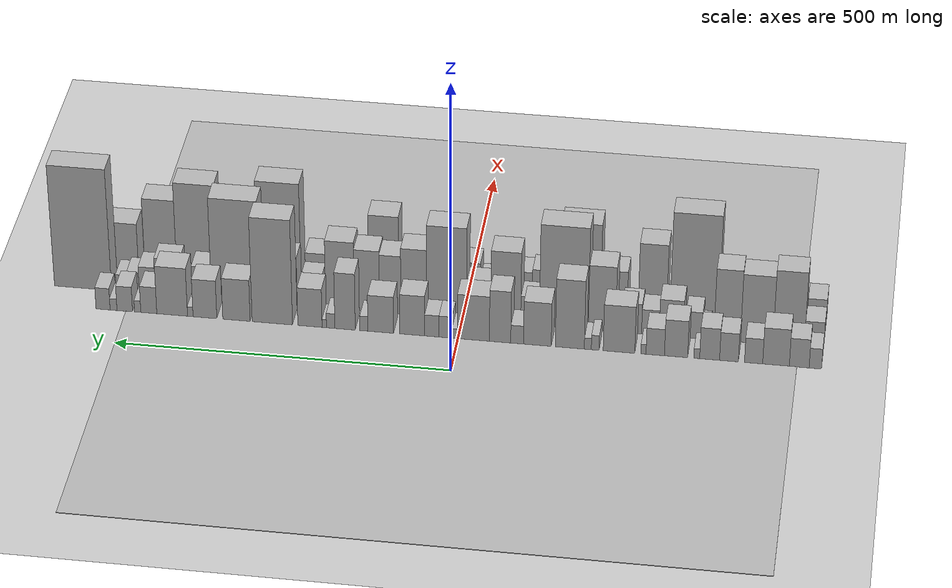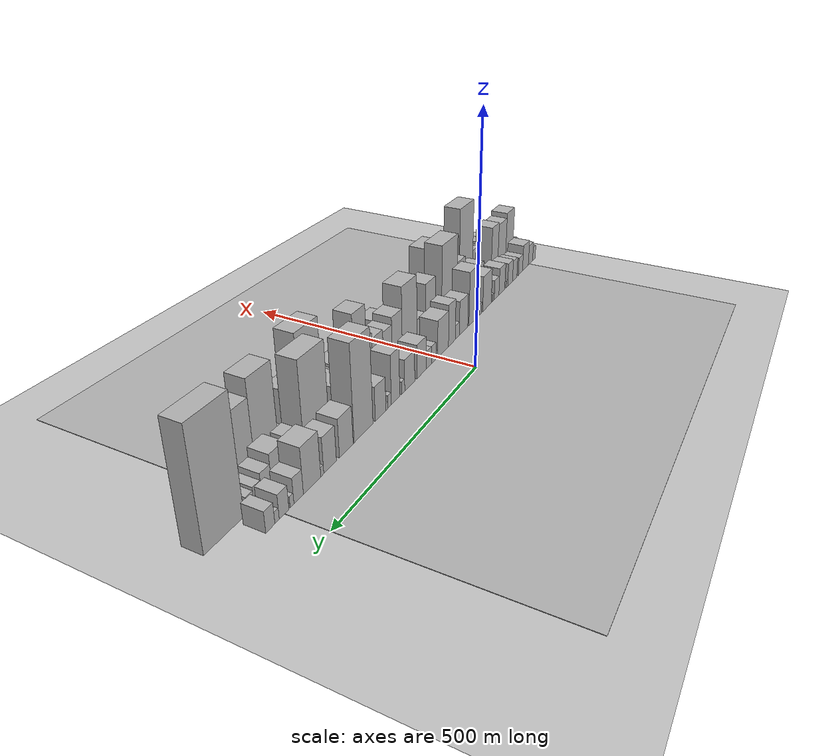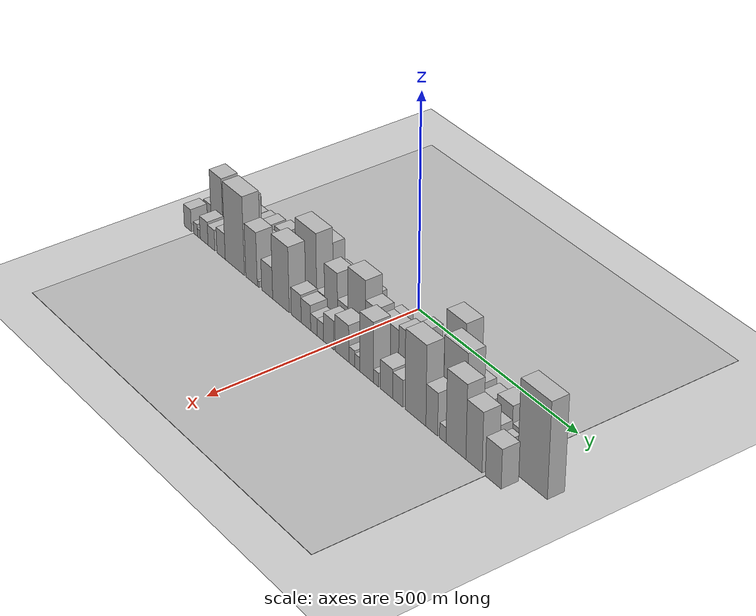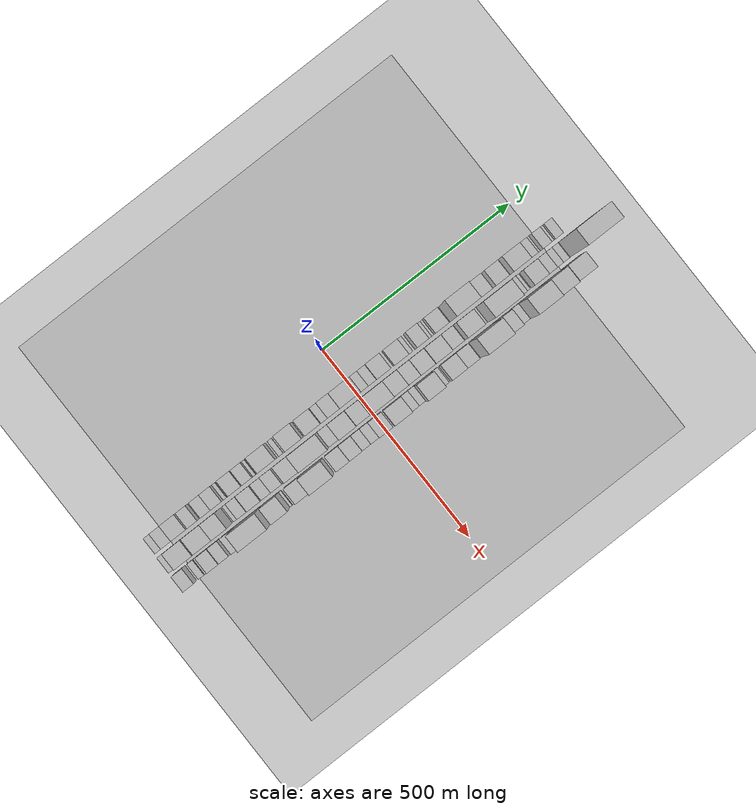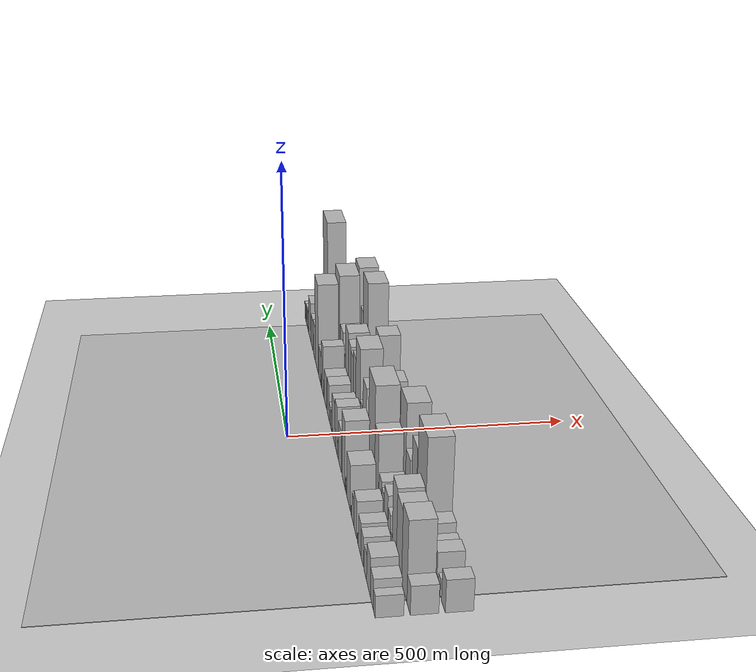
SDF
<?xml version="1.0" encoding="utf-8"?>

<sdf version="1.6">

   <world name="default">

      <gui fullscreen="0">

         <camera name="user_camera">

            <pose>-15 0 4.57585 0 0 0</pose>

            <view_controller>orbit</view_controller>

         </camera>

      </gui>

      <scene>

         <sky>

           <clouds>

             <speed>12</speed>

           </clouds>

         </sky>

         <ambient>0.4 0.4 0.4 1</ambient>

         <background>0.7 0.7 0.7 1</background>

         <shadows>1</shadows>

      </scene>

      <gravity>0 0 -9.8066</gravity>

      <magnetic_field>6e-06 2.3e-05 -4.2e-05</magnetic_field>

      <physics default="0" name="default_physics" type="ode">

         <ode>

            <solver>

               <type>quick</type>

               <iters>10</iters>

               <sor>1.0</sor>

               <use_dynamic_moi_rescaling>0</use_dynamic_moi_rescaling>

            </solver>

            <constraints>

               <cfm>0</cfm>

               <erp>0.2</erp>

               <contact_max_correcting_vel>100</contact_max_correcting_vel>

               <contact_surface_layer>0.001</contact_surface_layer>

            </constraints>

         </ode>

         <max_step_size>0.004</max_step_size>

         <real_time_factor>1</real_time_factor>

         <real_time_update_rate>250</real_time_update_rate>

      </physics>

      <light name="sun" type="directional">

         <cast_shadows>1</cast_shadows>

         <pose>0 0 10 0 0 0</pose>

         <diffuse>0.8 0.8 0.8 1</diffuse>

         <specular>0.2 0.2 0.2 1</specular>

         <attenuation>

            <range>1000</range>

            <constant>0.9</constant>

            <linear>0.01</linear>

            <quadratic>0.001</quadratic>

         </attenuation>

         <direction>-0.5 0.1 -0.9</direction>

      </light>

      <include>

         <name>ground_plane_1</name>

         <uri>model://HANNAS_ground_plane</uri>

         <pose>0 0 0  0 0 0</pose>

      </include>

      <include>

         <name>ground_plane_2</name>

         <uri>model://HANNAS_ground_plane</uri>

         <pose>100 0 0  0 0 0</pose>

      </include>

      <model name="building_1">

         <static>1</static>

         <pose frame="">100.0000 -526.9370 0 0.000000 0.000000 0.000000</pose>

         <link name="link">

            <pose frame="">0 0 18.00 0 0 0</pose>

            <collision name="collision">

               <geometry>

                  <box>

                     <size>40.0000 18.1259 36.0000</size>

                  </box>

               </geometry>

               <max_contacts>10</max_contacts>

               <surface>

                  <contact>

                     <ode/>

                  </contact>

                  <bounce/>

                  <friction>

                     <torsional>

                        <ode/>

                     </torsional>

                     <ode/>

                  </friction>

               </surface>

            </collision>

            <visual name="visual">

               <cast_shadows>0</cast_shadows>

               <geometry>

                  <box>

                     <size>40.0000 18.1259 36.0000</size>

                  </box>

               </geometry>

               <material>

                  <script>

                     <uri>model://HANNAS_wall/materials/scripts</uri>

                     <uri>model://HANNAS_wall/materials/textures</uri>

                     <name>vrc/HANNAS_wall</name>

                  </script>

               </material>

            </visual>

            <self_collide>0</self_collide>

            <enable_wind>0</enable_wind>

            <kinematic>0</kinematic>

         </link>

      </model>

      <model name="building_2">

         <static>1</static>

         <pose frame="">100.0000 -503.3876 0 0.000000 0.000000 0.000000</pose>

         <link name="link">

            <pose frame="">0 0 25.50 0 0 0</pose>

            <collision name="collision">

               <geometry>

                  <box>

                     <size>40.0000 28.9729 51.0000</size>

                  </box>

               </geometry>

               <max_contacts>10</max_contacts>

               <surface>

                  <contact>

                     <ode/>

                  </contact>

                  <bounce/>

                  <friction>

                     <torsional>

                        <ode/>

                     </torsional>

                     <ode/>

                  </friction>

               </surface>

            </collision>

            <visual name="visual">

               <cast_shadows>0</cast_shadows>

               <geometry>

                  <box>

                     <size>40.0000 28.9729 51.0000</size>

                  </box>

               </geometry>

               <material>

                  <script>

                     <uri>model://HANNAS_wall/materials/scripts</uri>

                     <uri>model://HANNAS_wall/materials/textures</uri>

                     <name>vrc/HANNAS_wall</name>

                  </script>

               </material>

            </visual>

            <self_collide>0</self_collide>

            <enable_wind>0</enable_wind>

            <kinematic>0</kinematic>

         </link>

      </model>

      <model name="building_3">

         <static>1</static>

         <pose frame="">100.0000 -469.4023 0 0.000000 0.000000 0.000000</pose>

         <link name="link">

            <pose frame="">0 0 33.00 0 0 0</pose>

            <collision name="collision">

               <geometry>

                  <box>

                     <size>40.0000 38.9977 66.0000</size>

                  </box>

               </geometry>

               <max_contacts>10</max_contacts>

               <surface>

                  <contact>

                     <ode/>

                  </contact>

                  <bounce/>

                  <friction>

                     <torsional>

                        <ode/>

                     </torsional>

                     <ode/>

                  </friction>

               </surface>

            </collision>

            <visual name="visual">

               <cast_shadows>0</cast_shadows>

               <geometry>

                  <box>

                     <size>40.0000 38.9977 66.0000</size>

                  </box>

               </geometry>

               <material>

                  <script>

                     <uri>model://HANNAS_wall/materials/scripts</uri>

                     <uri>model://HANNAS_wall/materials/textures</uri>

                     <name>vrc/HANNAS_wall</name>

                  </script>

               </material>

            </visual>

            <self_collide>0</self_collide>

            <enable_wind>0</enable_wind>

            <kinematic>0</kinematic>

         </link>

      </model>

      <model name="building_4">

         <static>1</static>

         <pose frame="">100.0000 -436.5735 0 0.000000 0.000000 0.000000</pose>

         <link name="link">

            <pose frame="">0 0 22.50 0 0 0</pose>

            <collision name="collision">

               <geometry>

                  <box>

                     <size>40.0000 26.6598 45.0000</size>

                  </box>

               </geometry>

               <max_contacts>10</max_contacts>

               <surface>

                  <contact>

                     <ode/>

                  </contact>

                  <bounce/>

                  <friction>

                     <torsional>

                        <ode/>

                     </torsional>

                     <ode/>

                  </friction>

               </surface>

            </collision>

            <visual name="visual">

               <cast_shadows>0</cast_shadows>

               <geometry>

                  <box>

                     <size>40.0000 26.6598 45.0000</size>

                  </box>

               </geometry>

               <material>

                  <script>

                     <uri>model://HANNAS_wall/materials/scripts</uri>

                     <uri>model://HANNAS_wall/materials/textures</uri>

                     <name>vrc/HANNAS_wall</name>

                  </script>

               </material>

            </visual>

            <self_collide>0</self_collide>

            <enable_wind>0</enable_wind>

            <kinematic>0</kinematic>

         </link>

      </model>

      <model name="building_5">

         <static>1</static>

         <pose frame="">100.0000 -400.4668 0 0.000000 0.000000 0.000000</pose>

         <link name="link">

            <pose frame="">0 0 25.50 0 0 0</pose>

            <collision name="collision">

               <geometry>

                  <box>

                     <size>40.0000 27.5535 51.0000</size>

                  </box>

               </geometry>

               <max_contacts>10</max_contacts>

               <surface>

                  <contact>

                     <ode/>

                  </contact>

                  <bounce/>

                  <friction>

                     <torsional>

                        <ode/>

                     </torsional>

                     <ode/>

                  </friction>

               </surface>

            </collision>

            <visual name="visual">

               <cast_shadows>0</cast_shadows>

               <geometry>

                  <box>

                     <size>40.0000 27.5535 51.0000</size>

                  </box>

               </geometry>

               <material>

                  <script>

                     <uri>model://HANNAS_wall/materials/scripts</uri>

                     <uri>model://HANNAS_wall/materials/textures</uri>

                     <name>vrc/HANNAS_wall</name>

                  </script>

               </material>

            </visual>

            <self_collide>0</self_collide>

            <enable_wind>0</enable_wind>

            <kinematic>0</kinematic>

         </link>

      </model>

      <model name="building_6">

         <static>1</static>

         <pose frame="">100.0000 -372.0732 0 0.000000 0.000000 0.000000</pose>

         <link name="link">

            <pose frame="">0 0 28.50 0 0 0</pose>

            <collision name="collision">

               <geometry>

                  <box>

                     <size>40.0000 29.2336 57.0000</size>

                  </box>

               </geometry>

               <max_contacts>10</max_contacts>

               <surface>

                  <contact>

                     <ode/>

                  </contact>

                  <bounce/>

                  <friction>

                     <torsional>

                        <ode/>

                     </torsional>

                     <ode/>

                  </friction>

               </surface>

            </collision>

            <visual name="visual">

               <cast_shadows>0</cast_shadows>

               <geometry>

                  <box>

                     <size>40.0000 29.2336 57.0000</size>

                  </box>

               </geometry>

               <material>

                  <script>

                     <uri>model://HANNAS_wall/materials/scripts</uri>

                     <uri>model://HANNAS_wall/materials/textures</uri>

                     <name>vrc/HANNAS_wall</name>

                  </script>

               </material>

            </visual>

            <self_collide>0</self_collide>

            <enable_wind>0</enable_wind>

            <kinematic>0</kinematic>

         </link>

      </model>

      <model name="building_7">

         <static>1</static>

         <pose frame="">100.0000 -353.0779 0 0.000000 0.000000 0.000000</pose>

         <link name="link">

            <pose frame="">0 0 9.00 0 0 0</pose>

            <collision name="collision">

               <geometry>

                  <box>

                     <size>40.0000 8.7571 18.0000</size>

                  </box>

               </geometry>

               <max_contacts>10</max_contacts>

               <surface>

                  <contact>

                     <ode/>

                  </contact>

                  <bounce/>

                  <friction>

                     <torsional>

                        <ode/>

                     </torsional>

                     <ode/>

                  </friction>

               </surface>

            </collision>

            <visual name="visual">

               <cast_shadows>0</cast_shadows>

               <geometry>

                  <box>

                     <size>40.0000 8.7571 18.0000</size>

                  </box>

               </geometry>

               <material>

                  <script>

                     <uri>model://HANNAS_wall/materials/scripts</uri>

                     <uri>model://HANNAS_wall/materials/textures</uri>

                     <name>vrc/HANNAS_wall</name>

                  </script>

               </material>

            </visual>

            <self_collide>0</self_collide>

            <enable_wind>0</enable_wind>

            <kinematic>0</kinematic>

         </link>

      </model>

      <model name="building_8">

         <static>1</static>

         <pose frame="">100.0000 -322.6337 0 0.000000 0.000000 0.000000</pose>

         <link name="link">

            <pose frame="">0 0 33.00 0 0 0</pose>

            <collision name="collision">

               <geometry>

                  <box>

                     <size>40.0000 34.1313 66.0000</size>

                  </box>

               </geometry>

               <max_contacts>10</max_contacts>

               <surface>

                  <contact>

                     <ode/>

                  </contact>

                  <bounce/>

                  <friction>

                     <torsional>

                        <ode/>

                     </torsional>

                     <ode/>

                  </friction>

               </surface>

            </collision>

            <visual name="visual">

               <cast_shadows>0</cast_shadows>

               <geometry>

                  <box>

                     <size>40.0000 34.1313 66.0000</size>

                  </box>

               </geometry>

               <material>

                  <script>

                     <uri>model://HANNAS_wall/materials/scripts</uri>

                     <uri>model://HANNAS_wall/materials/textures</uri>

                     <name>vrc/HANNAS_wall</name>

                  </script>

               </material>

            </visual>

            <self_collide>0</self_collide>

            <enable_wind>0</enable_wind>

            <kinematic>0</kinematic>

         </link>

      </model>

      <model name="building_9">

         <static>1</static>

         <pose frame="">100.0000 -292.0174 0 0.000000 0.000000 0.000000</pose>

         <link name="link">

            <pose frame="">0 0 24.00 0 0 0</pose>

            <collision name="collision">

               <geometry>

                  <box>

                     <size>40.0000 27.1014 48.0000</size>

                  </box>

               </geometry>

               <max_contacts>10</max_contacts>

               <surface>

                  <contact>

                     <ode/>

                  </contact>

                  <bounce/>

                  <friction>

                     <torsional>

                        <ode/>

                     </torsional>

                     <ode/>

                  </friction>

               </surface>

            </collision>

            <visual name="visual">

               <cast_shadows>0</cast_shadows>

               <geometry>

                  <box>

                     <size>40.0000 27.1014 48.0000</size>

                  </box>

               </geometry>

               <material>

                  <script>

                     <uri>model://HANNAS_wall/materials/scripts</uri>

                     <uri>model://HANNAS_wall/materials/textures</uri>

                     <name>vrc/HANNAS_wall</name>

                  </script>

               </material>

            </visual>

            <self_collide>0</self_collide>

            <enable_wind>0</enable_wind>

            <kinematic>0</kinematic>

         </link>

      </model>

      <model name="building_10">

         <static>1</static>

         <pose frame="">100.0000 -274.6580 0 0.000000 0.000000 0.000000</pose>

         <link name="link">

            <pose frame="">0 0 9.00 0 0 0</pose>

            <collision name="collision">

               <geometry>

                  <box>

                     <size>40.0000 7.6173 18.0000</size>

                  </box>

               </geometry>

               <max_contacts>10</max_contacts>

               <surface>

                  <contact>

                     <ode/>

                  </contact>

                  <bounce/>

                  <friction>

                     <torsional>

                        <ode/>

                     </torsional>

                     <ode/>

                  </friction>

               </surface>

            </collision>

            <visual name="visual">

               <cast_shadows>0</cast_shadows>

               <geometry>

                  <box>

                     <size>40.0000 7.6173 18.0000</size>

                  </box>

               </geometry>

               <material>

                  <script>

                     <uri>model://HANNAS_wall/materials/scripts</uri>

                     <uri>model://HANNAS_wall/materials/textures</uri>

                     <name>vrc/HANNAS_wall</name>

                  </script>

               </material>

            </visual>

            <self_collide>0</self_collide>

            <enable_wind>0</enable_wind>

            <kinematic>0</kinematic>

         </link>

      </model>

      <model name="building_11">

         <static>1</static>

         <pose frame="">100.0000 -238.5175 0 0.000000 0.000000 0.000000</pose>

         <link name="link">

            <pose frame="">0 0 42.00 0 0 0</pose>

            <collision name="collision">

               <geometry>

                  <box>

                     <size>40.0000 46.6637 84.0000</size>

                  </box>

               </geometry>

               <max_contacts>10</max_contacts>

               <surface>

                  <contact>

                     <ode/>

                  </contact>

                  <bounce/>

                  <friction>

                     <torsional>

                        <ode/>

                     </torsional>

                     <ode/>

                  </friction>

               </surface>

            </collision>

            <visual name="visual">

               <cast_shadows>0</cast_shadows>

               <geometry>

                  <box>

                     <size>40.0000 46.6637 84.0000</size>

                  </box>

               </geometry>

               <material>

                  <script>

                     <uri>model://HANNAS_wall/materials/scripts</uri>

                     <uri>model://HANNAS_wall/materials/textures</uri>

                     <name>vrc/HANNAS_wall</name>

                  </script>

               </material>

            </visual>

            <self_collide>0</self_collide>

            <enable_wind>0</enable_wind>

            <kinematic>0</kinematic>

         </link>

      </model>

      <model name="building_12">

         <static>1</static>

         <pose frame="">100.0000 -203.4173 0 0.000000 0.000000 0.000000</pose>

         <link name="link">

            <pose frame="">0 0 13.50 0 0 0</pose>

            <collision name="collision">

               <geometry>

                  <box>

                     <size>40.0000 11.5369 27.0000</size>

                  </box>

               </geometry>

               <max_contacts>10</max_contacts>

               <surface>

                  <contact>

                     <ode/>

                  </contact>

                  <bounce/>

                  <friction>

                     <torsional>

                        <ode/>

                     </torsional>

                     <ode/>

                  </friction>

               </surface>

            </collision>

            <visual name="visual">

               <cast_shadows>0</cast_shadows>

               <geometry>

                  <box>

                     <size>40.0000 11.5369 27.0000</size>

                  </box>

               </geometry>

               <material>

                  <script>

                     <uri>model://HANNAS_wall/materials/scripts</uri>

                     <uri>model://HANNAS_wall/materials/textures</uri>

                     <name>vrc/HANNAS_wall</name>

                  </script>

               </material>

            </visual>

            <self_collide>0</self_collide>

            <enable_wind>0</enable_wind>

            <kinematic>0</kinematic>

         </link>

      </model>

      <model name="building_13">

         <static>1</static>

         <pose frame="">100.0000 -192.4836 0 0.000000 0.000000 0.000000</pose>

         <link name="link">

            <pose frame="">0 0 10.50 0 0 0</pose>

            <collision name="collision">

               <geometry>

                  <box>

                     <size>40.0000 10.3304 21.0000</size>

                  </box>

               </geometry>

               <max_contacts>10</max_contacts>

               <surface>

                  <contact>

                     <ode/>

                  </contact>

                  <bounce/>

                  <friction>

                     <torsional>

                        <ode/>

                     </torsional>

                     <ode/>

                  </friction>

               </surface>

            </collision>

            <visual name="visual">

               <cast_shadows>0</cast_shadows>

               <geometry>

                  <box>

                     <size>40.0000 10.3304 21.0000</size>

                  </box>

               </geometry>

               <material>

                  <script>

                     <uri>model://HANNAS_wall/materials/scripts</uri>

                     <uri>model://HANNAS_wall/materials/textures</uri>

                     <name>vrc/HANNAS_wall</name>

                  </script>

               </material>

            </visual>

            <self_collide>0</self_collide>

            <enable_wind>0</enable_wind>

            <kinematic>0</kinematic>

         </link>

      </model>

      <model name="building_14">

         <static>1</static>

         <pose frame="">100.0000 -165.8141 0 0.000000 0.000000 0.000000</pose>

         <link name="link">

            <pose frame="">0 0 61.50 0 0 0</pose>

            <collision name="collision">

               <geometry>

                  <box>

                     <size>40.0000 43.0087 123.0000</size>

                  </box>

               </geometry>

               <max_contacts>10</max_contacts>

               <surface>

                  <contact>

                     <ode/>

                  </contact>

                  <bounce/>

                  <friction>

                     <torsional>

                        <ode/>

                     </torsional>

                     <ode/>

                  </friction>

               </surface>

            </collision>

            <visual name="visual">

               <cast_shadows>0</cast_shadows>

               <geometry>

                  <box>

                     <size>40.0000 43.0087 123.0000</size>

                  </box>

               </geometry>

               <material>

                  <script>

                     <uri>model://HANNAS_wall/materials/scripts</uri>

                     <uri>model://HANNAS_wall/materials/textures</uri>

                     <name>vrc/HANNAS_wall</name>

                  </script>

               </material>

            </visual>

            <self_collide>0</self_collide>

            <enable_wind>0</enable_wind>

            <kinematic>0</kinematic>

         </link>

      </model>

      <model name="building_15">

         <static>1</static>

         <pose frame="">100.0000 -117.7832 0 0.000000 0.000000 0.000000</pose>

         <link name="link">

            <pose frame="">0 0 39.00 0 0 0</pose>

            <collision name="collision">

               <geometry>

                  <box>

                     <size>40.0000 41.0529 78.0000</size>

                  </box>

               </geometry>

               <max_contacts>10</max_contacts>

               <surface>

                  <contact>

                     <ode/>

                  </contact>

                  <bounce/>

                  <friction>

                     <torsional>

                        <ode/>

                     </torsional>

                     <ode/>

                  </friction>

               </surface>

            </collision>

            <visual name="visual">

               <cast_shadows>0</cast_shadows>

               <geometry>

                  <box>

                     <size>40.0000 41.0529 78.0000</size>

                  </box>

               </geometry>

               <material>

                  <script>

                     <uri>model://HANNAS_wall/materials/scripts</uri>

                     <uri>model://HANNAS_wall/materials/textures</uri>

                     <name>vrc/HANNAS_wall</name>

                  </script>

               </material>

            </visual>

            <self_collide>0</self_collide>

            <enable_wind>0</enable_wind>

            <kinematic>0</kinematic>

         </link>

      </model>

      <model name="building_16">

         <static>1</static>

         <pose frame="">100.0000 -87.7702 0 0.000000 0.000000 0.000000</pose>

         <link name="link">

            <pose frame="">0 0 16.50 0 0 0</pose>

            <collision name="collision">

               <geometry>

                  <box>

                     <size>40.0000 18.9730 33.0000</size>

                  </box>

               </geometry>

               <max_contacts>10</max_contacts>

               <surface>

                  <contact>

                     <ode/>

                  </contact>

                  <bounce/>

                  <friction>

                     <torsional>

                        <ode/>

                     </torsional>

                     <ode/>

                  </friction>

               </surface>

            </collision>

            <visual name="visual">

               <cast_shadows>0</cast_shadows>

               <geometry>

                  <box>

                     <size>40.0000 18.9730 33.0000</size>

                  </box>

               </geometry>

               <material>

                  <script>

                     <uri>model://HANNAS_wall/materials/scripts</uri>

                     <uri>model://HANNAS_wall/materials/textures</uri>

                     <name>vrc/HANNAS_wall</name>

                  </script>

               </material>

            </visual>

            <self_collide>0</self_collide>

            <enable_wind>0</enable_wind>

            <kinematic>0</kinematic>

         </link>

      </model>

      <model name="building_17">

         <static>1</static>

         <pose frame="">100.0000 -62.4303 0 0.000000 0.000000 0.000000</pose>

         <link name="link">

            <pose frame="">0 0 46.50 0 0 0</pose>

            <collision name="collision">

               <geometry>

                  <box>

                     <size>40.0000 31.7069 93.0000</size>

                  </box>

               </geometry>

               <max_contacts>10</max_contacts>

               <surface>

                  <contact>

                     <ode/>

                  </contact>

                  <bounce/>

                  <friction>

                     <torsional>

                        <ode/>

                     </torsional>

                     <ode/>

                  </friction>

               </surface>

            </collision>

            <visual name="visual">

               <cast_shadows>0</cast_shadows>

               <geometry>

                  <box>

                     <size>40.0000 31.7069 93.0000</size>

                  </box>

               </geometry>

               <material>

                  <script>

                     <uri>model://HANNAS_wall/materials/scripts</uri>

                     <uri>model://HANNAS_wall/materials/textures</uri>

                     <name>vrc/HANNAS_wall</name>

                  </script>

               </material>

            </visual>

            <self_collide>0</self_collide>

            <enable_wind>0</enable_wind>

            <kinematic>0</kinematic>

         </link>

      </model>

      <model name="building_18">

         <static>1</static>

         <pose frame="">100.0000 -22.6745 0 0.000000 0.000000 0.000000</pose>

         <link name="link">

            <pose frame="">0 0 40.50 0 0 0</pose>

            <collision name="collision">

               <geometry>

                  <box>

                     <size>40.0000 47.8046 81.0000</size>

                  </box>

               </geometry>

               <max_contacts>10</max_contacts>

               <surface>

                  <contact>

                     <ode/>

                  </contact>

                  <bounce/>

                  <friction>

                     <torsional>

                        <ode/>

                     </torsional>

                     <ode/>

                  </friction>

               </surface>

            </collision>

            <visual name="visual">

               <cast_shadows>0</cast_shadows>

               <geometry>

                  <box>

                     <size>40.0000 47.8046 81.0000</size>

                  </box>

               </geometry>

               <material>

                  <script>

                     <uri>model://HANNAS_wall/materials/scripts</uri>

                     <uri>model://HANNAS_wall/materials/textures</uri>

                     <name>vrc/HANNAS_wall</name>

                  </script>

               </material>

            </visual>

            <self_collide>0</self_collide>

            <enable_wind>0</enable_wind>

            <kinematic>0</kinematic>

         </link>

      </model>

      <model name="building_19">

         <static>1</static>

         <pose frame="">100.0000 5.1420 0 0.000000 0.000000 0.000000</pose>

         <link name="link">

            <pose frame="">0 0 9.00 0 0 0</pose>

            <collision name="collision">

               <geometry>

                  <box>

                     <size>40.0000 7.8285 18.0000</size>

                  </box>

               </geometry>

               <max_contacts>10</max_contacts>

               <surface>

                  <contact>

                     <ode/>

                  </contact>

                  <bounce/>

                  <friction>

                     <torsional>

                        <ode/>

                     </torsional>

                     <ode/>

                  </friction>

               </surface>

            </collision>

            <visual name="visual">

               <cast_shadows>0</cast_shadows>

               <geometry>

                  <box>

                     <size>40.0000 7.8285 18.0000</size>

                  </box>

               </geometry>

               <material>

                  <script>

                     <uri>model://HANNAS_wall/materials/scripts</uri>

                     <uri>model://HANNAS_wall/materials/textures</uri>

                     <name>vrc/HANNAS_wall</name>

                  </script>

               </material>

            </visual>

            <self_collide>0</self_collide>

            <enable_wind>0</enable_wind>

            <kinematic>0</kinematic>

         </link>

      </model>

      <model name="building_20">

         <static>1</static>

         <pose frame="">100.0000 18.8325 0 0.000000 0.000000 0.000000</pose>

         <link name="link">

            <pose frame="">0 0 19.50 0 0 0</pose>

            <collision name="collision">

               <geometry>

                  <box>

                     <size>40.0000 19.5526 39.0000</size>

                  </box>

               </geometry>

               <max_contacts>10</max_contacts>

               <surface>

                  <contact>

                     <ode/>

                  </contact>

                  <bounce/>

                  <friction>

                     <torsional>

                        <ode/>

                     </torsional>

                     <ode/>

                  </friction>

               </surface>

            </collision>

            <visual name="visual">

               <cast_shadows>0</cast_shadows>

               <geometry>

                  <box>

                     <size>40.0000 19.5526 39.0000</size>

                  </box>

               </geometry>

               <material>

                  <script>

                     <uri>model://HANNAS_wall/materials/scripts</uri>

                     <uri>model://HANNAS_wall/materials/textures</uri>

                     <name>vrc/HANNAS_wall</name>

                  </script>

               </material>

            </visual>

            <self_collide>0</self_collide>

            <enable_wind>0</enable_wind>

            <kinematic>0</kinematic>

         </link>

      </model>

      <model name="building_21">

         <static>1</static>

         <pose frame="">100.0000 39.2823 0 0.000000 0.000000 0.000000</pose>

         <link name="link">

            <pose frame="">0 0 19.50 0 0 0</pose>

            <collision name="collision">

               <geometry>

                  <box>

                     <size>40.0000 21.3469 39.0000</size>

                  </box>

               </geometry>

               <max_contacts>10</max_contacts>

               <surface>

                  <contact>

                     <ode/>

                  </contact>

                  <bounce/>

                  <friction>

                     <torsional>

                        <ode/>

                     </torsional>

                     <ode/>

                  </friction>

               </surface>

            </collision>

            <visual name="visual">

               <cast_shadows>0</cast_shadows>

               <geometry>

                  <box>

                     <size>40.0000 21.3469 39.0000</size>

                  </box>

               </geometry>

               <material>

                  <script>

                     <uri>model://HANNAS_wall/materials/scripts</uri>

                     <uri>model://HANNAS_wall/materials/textures</uri>

                     <name>vrc/HANNAS_wall</name>

                  </script>

               </material>

            </visual>

            <self_collide>0</self_collide>

            <enable_wind>0</enable_wind>

            <kinematic>0</kinematic>

         </link>

      </model>

      <model name="building_22">

         <static>1</static>

         <pose frame="">100.0000 68.7046 0 0.000000 0.000000 0.000000</pose>

         <link name="link">

            <pose frame="">0 0 36.00 0 0 0</pose>

            <collision name="collision">

               <geometry>

                  <box>

                     <size>40.0000 37.4976 72.0000</size>

                  </box>

               </geometry>

               <max_contacts>10</max_contacts>

               <surface>

                  <contact>

                     <ode/>

                  </contact>

                  <bounce/>

                  <friction>

                     <torsional>

                        <ode/>

                     </torsional>

                     <ode/>

                  </friction>

               </surface>

            </collision>

            <visual name="visual">

               <cast_shadows>0</cast_shadows>

               <geometry>

                  <box>

                     <size>40.0000 37.4976 72.0000</size>

                  </box>

               </geometry>

               <material>

                  <script>

                     <uri>model://HANNAS_wall/materials/scripts</uri>

                     <uri>model://HANNAS_wall/materials/textures</uri>

                     <name>vrc/HANNAS_wall</name>

                  </script>

               </material>

            </visual>

            <self_collide>0</self_collide>

            <enable_wind>0</enable_wind>

            <kinematic>0</kinematic>

         </link>

      </model>

      <model name="building_23">

         <static>1</static>

         <pose frame="">100.0000 115.7143 0 0.000000 0.000000 0.000000</pose>

         <link name="link">

            <pose frame="">0 0 33.00 0 0 0</pose>

            <collision name="collision">

               <geometry>

                  <box>

                     <size>40.0000 38.5218 66.0000</size>

                  </box>

               </geometry>

               <max_contacts>10</max_contacts>

               <surface>

                  <contact>

                     <ode/>

                  </contact>

                  <bounce/>

                  <friction>

                     <torsional>

                        <ode/>

                     </torsional>

                     <ode/>

                  </friction>

               </surface>

            </collision>

            <visual name="visual">

               <cast_shadows>0</cast_shadows>

               <geometry>

                  <box>

                     <size>40.0000 38.5218 66.0000</size>

                  </box>

               </geometry>

               <material>

                  <script>

                     <uri>model://HANNAS_wall/materials/scripts</uri>

                     <uri>model://HANNAS_wall/materials/textures</uri>

                     <name>vrc/HANNAS_wall</name>

                  </script>

               </material>

            </visual>

            <self_collide>0</self_collide>

            <enable_wind>0</enable_wind>

            <kinematic>0</kinematic>

         </link>

      </model>

      <model name="building_24">

         <static>1</static>

         <pose frame="">100.0000 140.9108 0 0.000000 0.000000 0.000000</pose>

         <link name="link">

            <pose frame="">0 0 13.50 0 0 0</pose>

            <collision name="collision">

               <geometry>

                  <box>

                     <size>40.0000 11.8714 27.0000</size>

                  </box>

               </geometry>

               <max_contacts>10</max_contacts>

               <surface>

                  <contact>

                     <ode/>

                  </contact>

                  <bounce/>

                  <friction>

                     <torsional>

                        <ode/>

                     </torsional>

                     <ode/>

                  </friction>

               </surface>

            </collision>

            <visual name="visual">

               <cast_shadows>0</cast_shadows>

               <geometry>

                  <box>

                     <size>40.0000 11.8714 27.0000</size>

                  </box>

               </geometry>

               <material>

                  <script>

                     <uri>model://HANNAS_wall/materials/scripts</uri>

                     <uri>model://HANNAS_wall/materials/textures</uri>

                     <name>vrc/HANNAS_wall</name>

                  </script>

               </material>

            </visual>

            <self_collide>0</self_collide>

            <enable_wind>0</enable_wind>

            <kinematic>0</kinematic>

         </link>

      </model>

      <model name="building_25">

         <static>1</static>

         <pose frame="">100.0000 169.1480 0 0.000000 0.000000 0.000000</pose>

         <link name="link">

            <pose frame="">0 0 51.00 0 0 0</pose>

            <collision name="collision">

               <geometry>

                  <box>

                     <size>40.0000 30.6031 102.0000</size>

                  </box>

               </geometry>

               <max_contacts>10</max_contacts>

               <surface>

                  <contact>

                     <ode/>

                  </contact>

                  <bounce/>

                  <friction>

                     <torsional>

                        <ode/>

                     </torsional>

                     <ode/>

                  </friction>

               </surface>

            </collision>

            <visual name="visual">

               <cast_shadows>0</cast_shadows>

               <geometry>

                  <box>

                     <size>40.0000 30.6031 102.0000</size>

                  </box>

               </geometry>

               <material>

                  <script>

                     <uri>model://HANNAS_wall/materials/scripts</uri>

                     <uri>model://HANNAS_wall/materials/textures</uri>

                     <name>vrc/HANNAS_wall</name>

                  </script>

               </material>

            </visual>

            <self_collide>0</self_collide>

            <enable_wind>0</enable_wind>

            <kinematic>0</kinematic>

         </link>

      </model>

      <model name="building_26">

         <static>1</static>

         <pose frame="">100.0000 190.7650 0 0.000000 0.000000 0.000000</pose>

         <link name="link">

            <pose frame="">0 0 13.50 0 0 0</pose>

            <collision name="collision">

               <geometry>

                  <box>

                     <size>40.0000 12.6308 27.0000</size>

                  </box>

               </geometry>

               <max_contacts>10</max_contacts>

               <surface>

                  <contact>

                     <ode/>

                  </contact>

                  <bounce/>

                  <friction>

                     <torsional>

                        <ode/>

                     </torsional>

                     <ode/>

                  </friction>

               </surface>

            </collision>

            <visual name="visual">

               <cast_shadows>0</cast_shadows>

               <geometry>

                  <box>

                     <size>40.0000 12.6308 27.0000</size>

                  </box>

               </geometry>

               <material>

                  <script>

                     <uri>model://HANNAS_wall/materials/scripts</uri>

                     <uri>model://HANNAS_wall/materials/textures</uri>

                     <name>vrc/HANNAS_wall</name>

                  </script>

               </material>

            </visual>

            <self_collide>0</self_collide>

            <enable_wind>0</enable_wind>

            <kinematic>0</kinematic>

         </link>

      </model>

      <model name="building_27">

         <static>1</static>

         <pose frame="">100.0000 200.3613 0 0.000000 0.000000 0.000000</pose>

         <link name="link">

            <pose frame="">0 0 7.50 0 0 0</pose>

            <collision name="collision">

               <geometry>

                  <box>

                     <size>40.0000 6.5619 15.0000</size>

                  </box>

               </geometry>

               <max_contacts>10</max_contacts>

               <surface>

                  <contact>

                     <ode/>

                  </contact>

                  <bounce/>

                  <friction>

                     <torsional>

                        <ode/>

                     </torsional>

                     <ode/>

                  </friction>

               </surface>

            </collision>

            <visual name="visual">

               <cast_shadows>0</cast_shadows>

               <geometry>

                  <box>

                     <size>40.0000 6.5619 15.0000</size>

                  </box>

               </geometry>

               <material>

                  <script>

                     <uri>model://HANNAS_wall/materials/scripts</uri>

                     <uri>model://HANNAS_wall/materials/textures</uri>

                     <name>vrc/HANNAS_wall</name>

                  </script>

               </material>

            </visual>

            <self_collide>0</self_collide>

            <enable_wind>0</enable_wind>

            <kinematic>0</kinematic>

         </link>

      </model>

      <model name="building_28">

         <static>1</static>

         <pose frame="">100.0000 221.8432 0 0.000000 0.000000 0.000000</pose>

         <link name="link">

            <pose frame="">0 0 34.50 0 0 0</pose>

            <collision name="collision">

               <geometry>

                  <box>

                     <size>40.0000 36.4018 69.0000</size>

                  </box>

               </geometry>

               <max_contacts>10</max_contacts>

               <surface>

                  <contact>

                     <ode/>

                  </contact>

                  <bounce/>

                  <friction>

                     <torsional>

                        <ode/>

                     </torsional>

                     <ode/>

                  </friction>

               </surface>

            </collision>

            <visual name="visual">

               <cast_shadows>0</cast_shadows>

               <geometry>

                  <box>

                     <size>40.0000 36.4018 69.0000</size>

                  </box>

               </geometry>

               <material>

                  <script>

                     <uri>model://HANNAS_wall/materials/scripts</uri>

                     <uri>model://HANNAS_wall/materials/textures</uri>

                     <name>vrc/HANNAS_wall</name>

                  </script>

               </material>

            </visual>

            <self_collide>0</self_collide>

            <enable_wind>0</enable_wind>

            <kinematic>0</kinematic>

         </link>

      </model>

      <model name="building_29">

         <static>1</static>

         <pose frame="">100.0000 278.4300 0 0.000000 0.000000 0.000000</pose>

         <link name="link">

            <pose frame="">0 0 94.50 0 0 0</pose>

            <collision name="collision">

               <geometry>

                  <box>

                     <size>40.0000 60.7719 189.0000</size>

                  </box>

               </geometry>

               <max_contacts>10</max_contacts>

               <surface>

                  <contact>

                     <ode/>

                  </contact>

                  <bounce/>

                  <friction>

                     <torsional>

                        <ode/>

                     </torsional>

                     <ode/>

                  </friction>

               </surface>

            </collision>

            <visual name="visual">

               <cast_shadows>0</cast_shadows>

               <geometry>

                  <box>

                     <size>40.0000 60.7719 189.0000</size>

                  </box>

               </geometry>

               <material>

                  <script>

                     <uri>model://HANNAS_wall/materials/scripts</uri>

                     <uri>model://HANNAS_wall/materials/textures</uri>

                     <name>vrc/HANNAS_wall</name>

                  </script>

               </material>

            </visual>

            <self_collide>0</self_collide>

            <enable_wind>0</enable_wind>

            <kinematic>0</kinematic>

         </link>

      </model>

      <model name="building_30">

         <static>1</static>

         <pose frame="">100.0000 332.4769 0 0.000000 0.000000 0.000000</pose>

         <link name="link">

            <pose frame="">0 0 37.50 0 0 0</pose>

            <collision name="collision">

               <geometry>

                  <box>

                     <size>40.0000 41.3220 75.0000</size>

                  </box>

               </geometry>

               <max_contacts>10</max_contacts>

               <surface>

                  <contact>

                     <ode/>

                  </contact>

                  <bounce/>

                  <friction>

                     <torsional>

                        <ode/>

                     </torsional>

                     <ode/>

                  </friction>

               </surface>

            </collision>

            <visual name="visual">

               <cast_shadows>0</cast_shadows>

               <geometry>

                  <box>

                     <size>40.0000 41.3220 75.0000</size>

                  </box>

               </geometry>

               <material>

                  <script>

                     <uri>model://HANNAS_wall/materials/scripts</uri>

                     <uri>model://HANNAS_wall/materials/textures</uri>

                     <name>vrc/HANNAS_wall</name>

                  </script>

               </material>

            </visual>

            <self_collide>0</self_collide>

            <enable_wind>0</enable_wind>

            <kinematic>0</kinematic>

         </link>

      </model>

      <model name="building_31">

         <static>1</static>

         <pose frame="">100.0000 380.1412 0 0.000000 0.000000 0.000000</pose>

         <link name="link">

            <pose frame="">0 0 34.50 0 0 0</pose>

            <collision name="collision">

               <geometry>

                  <box>

                     <size>40.0000 36.0065 69.0000</size>

                  </box>

               </geometry>

               <max_contacts>10</max_contacts>

               <surface>

                  <contact>

                     <ode/>

                  </contact>

                  <bounce/>

                  <friction>

                     <torsional>

                        <ode/>

                     </torsional>

                     <ode/>

                  </friction>

               </surface>

            </collision>

            <visual name="visual">

               <cast_shadows>0</cast_shadows>

               <geometry>

                  <box>

                     <size>40.0000 36.0065 69.0000</size>

                  </box>

               </geometry>

               <material>

                  <script>

                     <uri>model://HANNAS_wall/materials/scripts</uri>

                     <uri>model://HANNAS_wall/materials/textures</uri>

                     <name>vrc/HANNAS_wall</name>

                  </script>

               </material>

            </visual>

            <self_collide>0</self_collide>

            <enable_wind>0</enable_wind>

            <kinematic>0</kinematic>

         </link>

      </model>

      <model name="building_32">

         <static>1</static>

         <pose frame="">100.0000 402.3121 0 0.000000 0.000000 0.000000</pose>

         <link name="link">

            <pose frame="">0 0 9.00 0 0 0</pose>

            <collision name="collision">

               <geometry>

                  <box>

                     <size>40.0000 8.3354 18.0000</size>

                  </box>

               </geometry>

               <max_contacts>10</max_contacts>

               <surface>

                  <contact>

                     <ode/>

                  </contact>

                  <bounce/>

                  <friction>

                     <torsional>

                        <ode/>

                     </torsional>

                     <ode/>

                  </friction>

               </surface>

            </collision>

            <visual name="visual">

               <cast_shadows>0</cast_shadows>

               <geometry>

                  <box>

                     <size>40.0000 8.3354 18.0000</size>

                  </box>

               </geometry>

               <material>

                  <script>

                     <uri>model://HANNAS_wall/materials/scripts</uri>

                     <uri>model://HANNAS_wall/materials/textures</uri>

                     <name>vrc/HANNAS_wall</name>

                  </script>

               </material>

            </visual>

            <self_collide>0</self_collide>

            <enable_wind>0</enable_wind>

            <kinematic>0</kinematic>

         </link>

      </model>

      <model name="building_33">

         <static>1</static>

         <pose frame="">100.0000 429.7398 0 0.000000 0.000000 0.000000</pose>

         <link name="link">

            <pose frame="">0 0 43.50 0 0 0</pose>

            <collision name="collision">

               <geometry>

                  <box>

                     <size>40.0000 46.5200 87.0000</size>

                  </box>

               </geometry>

               <max_contacts>10</max_contacts>

               <surface>

                  <contact>

                     <ode/>

                  </contact>

                  <bounce/>

                  <friction>

                     <torsional>

                        <ode/>

                     </torsional>

                     <ode/>

                  </friction>

               </surface>

            </collision>

            <visual name="visual">

               <cast_shadows>0</cast_shadows>

               <geometry>

                  <box>

                     <size>40.0000 46.5200 87.0000</size>

                  </box>

               </geometry>

               <material>

                  <script>

                     <uri>model://HANNAS_wall/materials/scripts</uri>

                     <uri>model://HANNAS_wall/materials/textures</uri>

                     <name>vrc/HANNAS_wall</name>

                  </script>

               </material>

            </visual>

            <self_collide>0</self_collide>

            <enable_wind>0</enable_wind>

            <kinematic>0</kinematic>

         </link>

      </model>

      <model name="building_34">

         <static>1</static>

         <pose frame="">100.0000 465.1372 0 0.000000 0.000000 0.000000</pose>

         <link name="link">

            <pose frame="">0 0 24.00 0 0 0</pose>

            <collision name="collision">

               <geometry>

                  <box>

                     <size>40.0000 24.2748 48.0000</size>

                  </box>

               </geometry>

               <max_contacts>10</max_contacts>

               <surface>

                  <contact>

                     <ode/>

                  </contact>

                  <bounce/>

                  <friction>

                     <torsional>

                        <ode/>

                     </torsional>

                     <ode/>

                  </friction>

               </surface>

            </collision>

            <visual name="visual">

               <cast_shadows>0</cast_shadows>

               <geometry>

                  <box>

                     <size>40.0000 24.2748 48.0000</size>

                  </box>

               </geometry>

               <material>

                  <script>

                     <uri>model://HANNAS_wall/materials/scripts</uri>

                     <uri>model://HANNAS_wall/materials/textures</uri>

                     <name>vrc/HANNAS_wall</name>

                  </script>

               </material>

            </visual>

            <self_collide>0</self_collide>

            <enable_wind>0</enable_wind>

            <kinematic>0</kinematic>

         </link>

      </model>

      <model name="building_35">

         <static>1</static>

         <pose frame="">100.0000 482.0341 0 0.000000 0.000000 0.000000</pose>

         <link name="link">

            <pose frame="">0 0 10.50 0 0 0</pose>

            <collision name="collision">

               <geometry>

                  <box>

                     <size>40.0000 9.5189 21.0000</size>

                  </box>

               </geometry>

               <max_contacts>10</max_contacts>

               <surface>

                  <contact>

                     <ode/>

                  </contact>

                  <bounce/>

                  <friction>

                     <torsional>

                        <ode/>

                     </torsional>

                     <ode/>

                  </friction>

               </surface>

            </collision>

            <visual name="visual">

               <cast_shadows>0</cast_shadows>

               <geometry>

                  <box>

                     <size>40.0000 9.5189 21.0000</size>

                  </box>

               </geometry>

               <material>

                  <script>

                     <uri>model://HANNAS_wall/materials/scripts</uri>

                     <uri>model://HANNAS_wall/materials/textures</uri>

                     <name>vrc/HANNAS_wall</name>

                  </script>

               </material>

            </visual>

            <self_collide>0</self_collide>

            <enable_wind>0</enable_wind>

            <kinematic>0</kinematic>

         </link>

      </model>

      <model name="building_36">

         <static>1</static>

         <pose frame="">100.0000 501.6301 0 0.000000 0.000000 0.000000</pose>

         <link name="link">

            <pose frame="">0 0 22.50 0 0 0</pose>

            <collision name="collision">

               <geometry>

                  <box>

                     <size>40.0000 23.6731 45.0000</size>

                  </box>

               </geometry>

               <max_contacts>10</max_contacts>

               <surface>

                  <contact>

                     <ode/>

                  </contact>

                  <bounce/>

                  <friction>

                     <torsional>

                        <ode/>

                     </torsional>

                     <ode/>

                  </friction>

               </surface>

            </collision>

            <visual name="visual">

               <cast_shadows>0</cast_shadows>

               <geometry>

                  <box>

                     <size>40.0000 23.6731 45.0000</size>

                  </box>

               </geometry>

               <material>

                  <script>

                     <uri>model://HANNAS_wall/materials/scripts</uri>

                     <uri>model://HANNAS_wall/materials/textures</uri>

                     <name>vrc/HANNAS_wall</name>

                  </script>

               </material>

            </visual>

            <self_collide>0</self_collide>

            <enable_wind>0</enable_wind>

            <kinematic>0</kinematic>

         </link>

      </model>

      <model name="building_37">

         <static>1</static>

         <pose frame="">100.0000 518.7028 0 0.000000 0.000000 0.000000</pose>

         <link name="link">

            <pose frame="">0 0 10.50 0 0 0</pose>

            <collision name="collision">

               <geometry>

                  <box>

                     <size>40.0000 10.4723 21.0000</size>

                  </box>

               </geometry>

               <max_contacts>10</max_contacts>

               <surface>

                  <contact>

                     <ode/>

                  </contact>

                  <bounce/>

                  <friction>

                     <torsional>

                        <ode/>

                     </torsional>

                     <ode/>

                  </friction>

               </surface>

            </collision>

            <visual name="visual">

               <cast_shadows>0</cast_shadows>

               <geometry>

                  <box>

                     <size>40.0000 10.4723 21.0000</size>

                  </box>

               </geometry>

               <material>

                  <script>

                     <uri>model://HANNAS_wall/materials/scripts</uri>

                     <uri>model://HANNAS_wall/materials/textures</uri>

                     <name>vrc/HANNAS_wall</name>

                  </script>

               </material>

            </visual>

            <self_collide>0</self_collide>

            <enable_wind>0</enable_wind>

            <kinematic>0</kinematic>

         </link>

      </model>

      <model name="building_38">

         <static>1</static>

         <pose frame="">100.0000 534.6236 0 0.000000 0.000000 0.000000</pose>

         <link name="link">

            <pose frame="">0 0 19.50 0 0 0</pose>

            <collision name="collision">

               <geometry>

                  <box>

                     <size>40.0000 21.3694 39.0000</size>

                  </box>

               </geometry>

               <max_contacts>10</max_contacts>

               <surface>

                  <contact>

                     <ode/>

                  </contact>

                  <bounce/>

                  <friction>

                     <torsional>

                        <ode/>

                     </torsional>

                     <ode/>

                  </friction>

               </surface>

            </collision>

            <visual name="visual">

               <cast_shadows>0</cast_shadows>

               <geometry>

                  <box>

                     <size>40.0000 21.3694 39.0000</size>

                  </box>

               </geometry>

               <material>

                  <script>

                     <uri>model://HANNAS_wall/materials/scripts</uri>

                     <uri>model://HANNAS_wall/materials/textures</uri>

                     <name>vrc/HANNAS_wall</name>

                  </script>

               </material>

            </visual>

            <self_collide>0</self_collide>

            <enable_wind>0</enable_wind>

            <kinematic>0</kinematic>

         </link>

      </model>

      <model name="building_39">

         <static>1</static>

         <pose frame="">149.0000 -521.7345 0 0.000000 0.000000 0.000000</pose>

         <link name="link">

            <pose frame="">0 0 24.00 0 0 0</pose>

            <collision name="collision">

               <geometry>

                  <box>

                     <size>40.0000 28.5310 48.0000</size>

                  </box>

               </geometry>

               <max_contacts>10</max_contacts>

               <surface>

                  <contact>

                     <ode/>

                  </contact>

                  <bounce/>

                  <friction>

                     <torsional>

                        <ode/>

                     </torsional>

                     <ode/>

                  </friction>

               </surface>

            </collision>

            <visual name="visual">

               <cast_shadows>0</cast_shadows>

               <geometry>

                  <box>

                     <size>40.0000 28.5310 48.0000</size>

                  </box>

               </geometry>

               <material>

                  <script>

                     <uri>model://HANNAS_wall/materials/scripts</uri>

                     <uri>model://HANNAS_wall/materials/textures</uri>

                     <name>vrc/HANNAS_wall</name>

                  </script>

               </material>

            </visual>

            <self_collide>0</self_collide>

            <enable_wind>0</enable_wind>

            <kinematic>0</kinematic>

         </link>

      </model>

      <model name="building_40">

         <static>1</static>

         <pose frame="">149.0000 -484.3753 0 0.000000 0.000000 0.000000</pose>

         <link name="link">

            <pose frame="">0 0 67.50 0 0 0</pose>

            <collision name="collision">

               <geometry>

                  <box>

                     <size>40.0000 46.1875 135.0000</size>

                  </box>

               </geometry>

               <max_contacts>10</max_contacts>

               <surface>

                  <contact>

                     <ode/>

                  </contact>

                  <bounce/>

                  <friction>

                     <torsional>

                        <ode/>

                     </torsional>

                     <ode/>

                  </friction>

               </surface>

            </collision>

            <visual name="visual">

               <cast_shadows>0</cast_shadows>

               <geometry>

                  <box>

                     <size>40.0000 46.1875 135.0000</size>

                  </box>

               </geometry>

               <material>

                  <script>

                     <uri>model://HANNAS_wall/materials/scripts</uri>

                     <uri>model://HANNAS_wall/materials/textures</uri>

                     <name>vrc/HANNAS_wall</name>

                  </script>

               </material>

            </visual>

            <self_collide>0</self_collide>

            <enable_wind>0</enable_wind>

            <kinematic>0</kinematic>

         </link>

      </model>

      <model name="building_41">

         <static>1</static>

         <pose frame="">149.0000 -437.2656 0 0.000000 0.000000 0.000000</pose>

         <link name="link">

            <pose frame="">0 0 61.50 0 0 0</pose>

            <collision name="collision">

               <geometry>

                  <box>

                     <size>40.0000 48.0318 123.0000</size>

                  </box>

               </geometry>

               <max_contacts>10</max_contacts>

               <surface>

                  <contact>

                     <ode/>

                  </contact>

                  <bounce/>

                  <friction>

                     <torsional>

                        <ode/>

                     </torsional>

                     <ode/>

                  </friction>

               </surface>

            </collision>

            <visual name="visual">

               <cast_shadows>0</cast_shadows>

               <geometry>

                  <box>

                     <size>40.0000 48.0318 123.0000</size>

                  </box>

               </geometry>

               <material>

                  <script>

                     <uri>model://HANNAS_wall/materials/scripts</uri>

                     <uri>model://HANNAS_wall/materials/textures</uri>

                     <name>vrc/HANNAS_wall</name>

                  </script>

               </material>

            </visual>

            <self_collide>0</self_collide>

            <enable_wind>0</enable_wind>

            <kinematic>0</kinematic>

         </link>

      </model>

      <model name="building_42">

         <static>1</static>

         <pose frame="">149.0000 -393.5932 0 0.000000 0.000000 0.000000</pose>

         <link name="link">

            <pose frame="">0 0 64.50 0 0 0</pose>

            <collision name="collision">

               <geometry>

                  <box>

                     <size>40.0000 39.3130 129.0000</size>

                  </box>

               </geometry>

               <max_contacts>10</max_contacts>

               <surface>

                  <contact>

                     <ode/>

                  </contact>

                  <bounce/>

                  <friction>

                     <torsional>

                        <ode/>

                     </torsional>

                     <ode/>

                  </friction>

               </surface>

            </collision>

            <visual name="visual">

               <cast_shadows>0</cast_shadows>

               <geometry>

                  <box>

                     <size>40.0000 39.3130 129.0000</size>

                  </box>

               </geometry>

               <material>

                  <script>

                     <uri>model://HANNAS_wall/materials/scripts</uri>

                     <uri>model://HANNAS_wall/materials/textures</uri>

                     <name>vrc/HANNAS_wall</name>

                  </script>

               </material>

            </visual>

            <self_collide>0</self_collide>

            <enable_wind>0</enable_wind>

            <kinematic>0</kinematic>

         </link>

      </model>

      <model name="building_43">

         <static>1</static>

         <pose frame="">149.0000 -362.1825 0 0.000000 0.000000 0.000000</pose>

         <link name="link">

            <pose frame="">0 0 12.00 0 0 0</pose>

            <collision name="collision">

               <geometry>

                  <box>

                     <size>40.0000 11.5084 24.0000</size>

                  </box>

               </geometry>

               <max_contacts>10</max_contacts>

               <surface>

                  <contact>

                     <ode/>

                  </contact>

                  <bounce/>

                  <friction>

                     <torsional>

                        <ode/>

                     </torsional>

                     <ode/>

                  </friction>

               </surface>

            </collision>

            <visual name="visual">

               <cast_shadows>0</cast_shadows>

               <geometry>

                  <box>

                     <size>40.0000 11.5084 24.0000</size>

                  </box>

               </geometry>

               <material>

                  <script>

                     <uri>model://HANNAS_wall/materials/scripts</uri>

                     <uri>model://HANNAS_wall/materials/textures</uri>

                     <name>vrc/HANNAS_wall</name>

                  </script>

               </material>

            </visual>

            <self_collide>0</self_collide>

            <enable_wind>0</enable_wind>

            <kinematic>0</kinematic>

         </link>

      </model>

      <model name="building_44">

         <static>1</static>

         <pose frame="">149.0000 -344.1168 0 0.000000 0.000000 0.000000</pose>

         <link name="link">

            <pose frame="">0 0 24.00 0 0 0</pose>

            <collision name="collision">

               <geometry>

                  <box>

                     <size>40.0000 24.6230 48.0000</size>

                  </box>

               </geometry>

               <max_contacts>10</max_contacts>

               <surface>

                  <contact>

                     <ode/>

                  </contact>

                  <bounce/>

                  <friction>

                     <torsional>

                        <ode/>

                     </torsional>

                     <ode/>

                  </friction>

               </surface>

            </collision>

            <visual name="visual">

               <cast_shadows>0</cast_shadows>

               <geometry>

                  <box>

                     <size>40.0000 24.6230 48.0000</size>

                  </box>

               </geometry>

               <material>

                  <script>

                     <uri>model://HANNAS_wall/materials/scripts</uri>

                     <uri>model://HANNAS_wall/materials/textures</uri>

                     <name>vrc/HANNAS_wall</name>

                  </script>

               </material>

            </visual>

            <self_collide>0</self_collide>

            <enable_wind>0</enable_wind>

            <kinematic>0</kinematic>

         </link>

      </model>

      <model name="building_45">

         <static>1</static>

         <pose frame="">149.0000 -310.9780 0 0.000000 0.000000 0.000000</pose>

         <link name="link">

            <pose frame="">0 0 33.00 0 0 0</pose>

            <collision name="collision">

               <geometry>

                  <box>

                     <size>40.0000 35.6545 66.0000</size>

                  </box>

               </geometry>

               <max_contacts>10</max_contacts>

               <surface>

                  <contact>

                     <ode/>

                  </contact>

                  <bounce/>

                  <friction>

                     <torsional>

                        <ode/>

                     </torsional>

                     <ode/>

                  </friction>

               </surface>

            </collision>

            <visual name="visual">

               <cast_shadows>0</cast_shadows>

               <geometry>

                  <box>

                     <size>40.0000 35.6545 66.0000</size>

                  </box>

               </geometry>

               <material>

                  <script>

                     <uri>model://HANNAS_wall/materials/scripts</uri>

                     <uri>model://HANNAS_wall/materials/textures</uri>

                     <name>vrc/HANNAS_wall</name>

                  </script>

               </material>

            </visual>

            <self_collide>0</self_collide>

            <enable_wind>0</enable_wind>

            <kinematic>0</kinematic>

         </link>

      </model>

      <model name="building_46">

         <static>1</static>

         <pose frame="">149.0000 -280.0862 0 0.000000 0.000000 0.000000</pose>

         <link name="link">

            <pose frame="">0 0 22.50 0 0 0</pose>

            <collision name="collision">

               <geometry>

                  <box>

                     <size>40.0000 26.1290 45.0000</size>

                  </box>

               </geometry>

               <max_contacts>10</max_contacts>

               <surface>

                  <contact>

                     <ode/>

                  </contact>

                  <bounce/>

                  <friction>

                     <torsional>

                        <ode/>

                     </torsional>

                     <ode/>

                  </friction>

               </surface>

            </collision>

            <visual name="visual">

               <cast_shadows>0</cast_shadows>

               <geometry>

                  <box>

                     <size>40.0000 26.1290 45.0000</size>

                  </box>

               </geometry>

               <material>

                  <script>

                     <uri>model://HANNAS_wall/materials/scripts</uri>

                     <uri>model://HANNAS_wall/materials/textures</uri>

                     <name>vrc/HANNAS_wall</name>

                  </script>

               </material>

            </visual>

            <self_collide>0</self_collide>

            <enable_wind>0</enable_wind>

            <kinematic>0</kinematic>

         </link>

      </model>

      <model name="building_47">

         <static>1</static>

         <pose frame="">149.0000 -252.2133 0 0.000000 0.000000 0.000000</pose>

         <link name="link">

            <pose frame="">0 0 27.00 0 0 0</pose>

            <collision name="collision">

               <geometry>

                  <box>

                     <size>40.0000 29.6169 54.0000</size>

                  </box>

               </geometry>

               <max_contacts>10</max_contacts>

               <surface>

                  <contact>

                     <ode/>

                  </contact>

                  <bounce/>

                  <friction>

                     <torsional>

                        <ode/>

                     </torsional>

                     <ode/>

                  </friction>

               </surface>

            </collision>

            <visual name="visual">

               <cast_shadows>0</cast_shadows>

               <geometry>

                  <box>

                     <size>40.0000 29.6169 54.0000</size>

                  </box>

               </geometry>

               <material>

                  <script>

                     <uri>model://HANNAS_wall/materials/scripts</uri>

                     <uri>model://HANNAS_wall/materials/textures</uri>

                     <name>vrc/HANNAS_wall</name>

                  </script>

               </material>

            </visual>

            <self_collide>0</self_collide>

            <enable_wind>0</enable_wind>

            <kinematic>0</kinematic>

         </link>

      </model>

      <model name="building_48">

         <static>1</static>

         <pose frame="">149.0000 -208.0061 0 0.000000 0.000000 0.000000</pose>

         <link name="link">

            <pose frame="">0 0 58.50 0 0 0</pose>

            <collision name="collision">

               <geometry>

                  <box>

                     <size>40.0000 40.7973 117.0000</size>

                  </box>

               </geometry>

               <max_contacts>10</max_contacts>

               <surface>

                  <contact>

                     <ode/>

                  </contact>

                  <bounce/>

                  <friction>

                     <torsional>

                        <ode/>

                     </torsional>

                     <ode/>

                  </friction>

               </surface>

            </collision>

            <visual name="visual">

               <cast_shadows>0</cast_shadows>

               <geometry>

                  <box>

                     <size>40.0000 40.7973 117.0000</size>

                  </box>

               </geometry>

               <material>

                  <script>

                     <uri>model://HANNAS_wall/materials/scripts</uri>

                     <uri>model://HANNAS_wall/materials/textures</uri>

                     <name>vrc/HANNAS_wall</name>

                  </script>

               </material>

            </visual>

            <self_collide>0</self_collide>

            <enable_wind>0</enable_wind>

            <kinematic>0</kinematic>

         </link>

      </model>

      <model name="building_49">

         <static>1</static>

         <pose frame="">149.0000 -151.1907 0 0.000000 0.000000 0.000000</pose>

         <link name="link">

            <pose frame="">0 0 91.50 0 0 0</pose>

            <collision name="collision">

               <geometry>

                  <box>

                     <size>40.0000 72.8335 183.0000</size>

                  </box>

               </geometry>

               <max_contacts>10</max_contacts>

               <surface>

                  <contact>

                     <ode/>

                  </contact>

                  <bounce/>

                  <friction>

                     <torsional>

                        <ode/>

                     </torsional>

                     <ode/>

                  </friction>

               </surface>

            </collision>

            <visual name="visual">

               <cast_shadows>0</cast_shadows>

               <geometry>

                  <box>

                     <size>40.0000 72.8335 183.0000</size>

                  </box>

               </geometry>

               <material>

                  <script>

                     <uri>model://HANNAS_wall/materials/scripts</uri>

                     <uri>model://HANNAS_wall/materials/textures</uri>

                     <name>vrc/HANNAS_wall</name>

                  </script>

               </material>

            </visual>

            <self_collide>0</self_collide>

            <enable_wind>0</enable_wind>

            <kinematic>0</kinematic>

         </link>

      </model>

      <model name="building_50">

         <static>1</static>

         <pose frame="">149.0000 -100.8698 0 0.000000 0.000000 0.000000</pose>

         <link name="link">

            <pose frame="">0 0 25.50 0 0 0</pose>

            <collision name="collision">

               <geometry>

                  <box>

                     <size>40.0000 27.8084 51.0000</size>

                  </box>

               </geometry>

               <max_contacts>10</max_contacts>

               <surface>

                  <contact>

                     <ode/>

                  </contact>

                  <bounce/>

                  <friction>

                     <torsional>

                        <ode/>

                     </torsional>

                     <ode/>

                  </friction>

               </surface>

            </collision>

            <visual name="visual">

               <cast_shadows>0</cast_shadows>

               <geometry>

                  <box>

                     <size>40.0000 27.8084 51.0000</size>

                  </box>

               </geometry>

               <material>

                  <script>

                     <uri>model://HANNAS_wall/materials/scripts</uri>

                     <uri>model://HANNAS_wall/materials/textures</uri>

                     <name>vrc/HANNAS_wall</name>

                  </script>

               </material>

            </visual>

            <self_collide>0</self_collide>

            <enable_wind>0</enable_wind>

            <kinematic>0</kinematic>

         </link>

      </model>

      <model name="building_51">

         <static>1</static>

         <pose frame="">149.0000 -64.5780 0 0.000000 0.000000 0.000000</pose>

         <link name="link">

            <pose frame="">0 0 64.50 0 0 0</pose>

            <collision name="collision">

               <geometry>

                  <box>

                     <size>40.0000 44.7751 129.0000</size>

                  </box>

               </geometry>

               <max_contacts>10</max_contacts>

               <surface>

                  <contact>

                     <ode/>

                  </contact>

                  <bounce/>

                  <friction>

                     <torsional>

                        <ode/>

                     </torsional>

                     <ode/>

                  </friction>

               </surface>

            </collision>

            <visual name="visual">

               <cast_shadows>0</cast_shadows>

               <geometry>

                  <box>

                     <size>40.0000 44.7751 129.0000</size>

                  </box>

               </geometry>

               <material>

                  <script>

                     <uri>model://HANNAS_wall/materials/scripts</uri>

                     <uri>model://HANNAS_wall/materials/textures</uri>

                     <name>vrc/HANNAS_wall</name>

                  </script>

               </material>

            </visual>

            <self_collide>0</self_collide>

            <enable_wind>0</enable_wind>

            <kinematic>0</kinematic>

         </link>

      </model>

      <model name="building_52">

         <static>1</static>

         <pose frame="">149.0000 -23.9826 0 0.000000 0.000000 0.000000</pose>

         <link name="link">

            <pose frame="">0 0 34.50 0 0 0</pose>

            <collision name="collision">

               <geometry>

                  <box>

                     <size>40.0000 36.4156 69.0000</size>

                  </box>

               </geometry>

               <max_contacts>10</max_contacts>

               <surface>

                  <contact>

                     <ode/>

                  </contact>

                  <bounce/>

                  <friction>

                     <torsional>

                        <ode/>

                     </torsional>

                     <ode/>

                  </friction>

               </surface>

            </collision>

            <visual name="visual">

               <cast_shadows>0</cast_shadows>

               <geometry>

                  <box>

                     <size>40.0000 36.4156 69.0000</size>

                  </box>

               </geometry>

               <material>

                  <script>

                     <uri>model://HANNAS_wall/materials/scripts</uri>

                     <uri>model://HANNAS_wall/materials/textures</uri>

                     <name>vrc/HANNAS_wall</name>

                  </script>

               </material>

            </visual>

            <self_collide>0</self_collide>

            <enable_wind>0</enable_wind>

            <kinematic>0</kinematic>

         </link>

      </model>

      <model name="building_53">

         <static>1</static>

         <pose frame="">149.0000 24.1453 0 0.000000 0.000000 0.000000</pose>

         <link name="link">

            <pose frame="">0 0 82.50 0 0 0</pose>

            <collision name="collision">

               <geometry>

                  <box>

                     <size>40.0000 59.8403 165.0000</size>

                  </box>

               </geometry>

               <max_contacts>10</max_contacts>

               <surface>

                  <contact>

                     <ode/>

                  </contact>

                  <bounce/>

                  <friction>

                     <torsional>

                        <ode/>

                     </torsional>

                     <ode/>

                  </friction>

               </surface>

            </collision>

            <visual name="visual">

               <cast_shadows>0</cast_shadows>

               <geometry>

                  <box>

                     <size>40.0000 59.8403 165.0000</size>

                  </box>

               </geometry>

               <material>

                  <script>

                     <uri>model://HANNAS_wall/materials/scripts</uri>

                     <uri>model://HANNAS_wall/materials/textures</uri>

                     <name>vrc/HANNAS_wall</name>

                  </script>

               </material>

            </visual>

            <self_collide>0</self_collide>

            <enable_wind>0</enable_wind>

            <kinematic>0</kinematic>

         </link>

      </model>

      <model name="building_54">

         <static>1</static>

         <pose frame="">149.0000 73.3788 0 0.000000 0.000000 0.000000</pose>

         <link name="link">

            <pose frame="">0 0 60.00 0 0 0</pose>

            <collision name="collision">

               <geometry>

                  <box>

                     <size>40.0000 38.6266 120.0000</size>

                  </box>

               </geometry>

               <max_contacts>10</max_contacts>

               <surface>

                  <contact>

                     <ode/>

                  </contact>

                  <bounce/>

                  <friction>

                     <torsional>

                        <ode/>

                     </torsional>

                     <ode/>

                  </friction>

               </surface>

            </collision>

            <visual name="visual">

               <cast_shadows>0</cast_shadows>

               <geometry>

                  <box>

                     <size>40.0000 38.6266 120.0000</size>

                  </box>

               </geometry>

               <material>

                  <script>

                     <uri>model://HANNAS_wall/materials/scripts</uri>

                     <uri>model://HANNAS_wall/materials/textures</uri>

                     <name>vrc/HANNAS_wall</name>

                  </script>

               </material>

            </visual>

            <self_collide>0</self_collide>

            <enable_wind>0</enable_wind>

            <kinematic>0</kinematic>

         </link>

      </model>

      <model name="building_55">

         <static>1</static>

         <pose frame="">149.0000 108.8950 0 0.000000 0.000000 0.000000</pose>

         <link name="link">

            <pose frame="">0 0 52.50 0 0 0</pose>

            <collision name="collision">

               <geometry>

                  <box>

                     <size>40.0000 32.4059 105.0000</size>

                  </box>

               </geometry>

               <max_contacts>10</max_contacts>

               <surface>

                  <contact>

                     <ode/>

                  </contact>

                  <bounce/>

                  <friction>

                     <torsional>

                        <ode/>

                     </torsional>

                     <ode/>

                  </friction>

               </surface>

            </collision>

            <visual name="visual">

               <cast_shadows>0</cast_shadows>

               <geometry>

                  <box>

                     <size>40.0000 32.4059 105.0000</size>

                  </box>

               </geometry>

               <material>

                  <script>

                     <uri>model://HANNAS_wall/materials/scripts</uri>

                     <uri>model://HANNAS_wall/materials/textures</uri>

                     <name>vrc/HANNAS_wall</name>

                  </script>

               </material>

            </visual>

            <self_collide>0</self_collide>

            <enable_wind>0</enable_wind>

            <kinematic>0</kinematic>

         </link>

      </model>

      <model name="building_56">

         <static>1</static>

         <pose frame="">149.0000 144.0499 0 0.000000 0.000000 0.000000</pose>

         <link name="link">

            <pose frame="">0 0 55.50 0 0 0</pose>

            <collision name="collision">

               <geometry>

                  <box>

                     <size>40.0000 37.9039 111.0000</size>

                  </box>

               </geometry>

               <max_contacts>10</max_contacts>

               <surface>

                  <contact>

                     <ode/>

                  </contact>

                  <bounce/>

                  <friction>

                     <torsional>

                        <ode/>

                     </torsional>

                     <ode/>

                  </friction>

               </surface>

            </collision>

            <visual name="visual">

               <cast_shadows>0</cast_shadows>

               <geometry>

                  <box>

                     <size>40.0000 37.9039 111.0000</size>

                  </box>

               </geometry>

               <material>

                  <script>

                     <uri>model://HANNAS_wall/materials/scripts</uri>

                     <uri>model://HANNAS_wall/materials/textures</uri>

                     <name>vrc/HANNAS_wall</name>

                  </script>

               </material>

            </visual>

            <self_collide>0</self_collide>

            <enable_wind>0</enable_wind>

            <kinematic>0</kinematic>

         </link>

      </model>

      <model name="building_57">

         <static>1</static>

         <pose frame="">149.0000 184.5599 0 0.000000 0.000000 0.000000</pose>

         <link name="link">

            <pose frame="">0 0 61.50 0 0 0</pose>

            <collision name="collision">

               <geometry>

                  <box>

                     <size>40.0000 43.1160 123.0000</size>

                  </box>

               </geometry>

               <max_contacts>10</max_contacts>

               <surface>

                  <contact>

                     <ode/>

                  </contact>

                  <bounce/>

                  <friction>

                     <torsional>

                        <ode/>

                     </torsional>

                     <ode/>

                  </friction>

               </surface>

            </collision>

            <visual name="visual">

               <cast_shadows>0</cast_shadows>

               <geometry>

                  <box>

                     <size>40.0000 43.1160 123.0000</size>

                  </box>

               </geometry>

               <material>

                  <script>

                     <uri>model://HANNAS_wall/materials/scripts</uri>

                     <uri>model://HANNAS_wall/materials/textures</uri>

                     <name>vrc/HANNAS_wall</name>

                  </script>

               </material>

            </visual>

            <self_collide>0</self_collide>

            <enable_wind>0</enable_wind>

            <kinematic>0</kinematic>

         </link>

      </model>

      <model name="building_58">

         <static>1</static>

         <pose frame="">149.0000 227.6423 0 0.000000 0.000000 0.000000</pose>

         <link name="link">

            <pose frame="">0 0 27.00 0 0 0</pose>

            <collision name="collision">

               <geometry>

                  <box>

                     <size>40.0000 31.0489 54.0000</size>

                  </box>

               </geometry>

               <max_contacts>10</max_contacts>

               <surface>

                  <contact>

                     <ode/>

                  </contact>

                  <bounce/>

                  <friction>

                     <torsional>

                        <ode/>

                     </torsional>

                     <ode/>

                  </friction>

               </surface>

            </collision>

            <visual name="visual">

               <cast_shadows>0</cast_shadows>

               <geometry>

                  <box>

                     <size>40.0000 31.0489 54.0000</size>

                  </box>

               </geometry>

               <material>

                  <script>

                     <uri>model://HANNAS_wall/materials/scripts</uri>

                     <uri>model://HANNAS_wall/materials/textures</uri>

                     <name>vrc/HANNAS_wall</name>

                  </script>

               </material>

            </visual>

            <self_collide>0</self_collide>

            <enable_wind>0</enable_wind>

            <kinematic>0</kinematic>

         </link>

      </model>

      <model name="building_59">

         <static>1</static>

         <pose frame="">149.0000 272.0626 0 0.000000 0.000000 0.000000</pose>

         <link name="link">

            <pose frame="">0 0 43.50 0 0 0</pose>

            <collision name="collision">

               <geometry>

                  <box>

                     <size>40.0000 45.7917 87.0000</size>

                  </box>

               </geometry>

               <max_contacts>10</max_contacts>

               <surface>

                  <contact>

                     <ode/>

                  </contact>

                  <bounce/>

                  <friction>

                     <torsional>

                        <ode/>

                     </torsional>

                     <ode/>

                  </friction>

               </surface>

            </collision>

            <visual name="visual">

               <cast_shadows>0</cast_shadows>

               <geometry>

                  <box>

                     <size>40.0000 45.7917 87.0000</size>

                  </box>

               </geometry>

               <material>

                  <script>

                     <uri>model://HANNAS_wall/materials/scripts</uri>

                     <uri>model://HANNAS_wall/materials/textures</uri>

                     <name>vrc/HANNAS_wall</name>

                  </script>

               </material>

            </visual>

            <self_collide>0</self_collide>

            <enable_wind>0</enable_wind>

            <kinematic>0</kinematic>

         </link>

      </model>

      <model name="building_60">

         <static>1</static>

         <pose frame="">149.0000 300.8879 0 0.000000 0.000000 0.000000</pose>

         <link name="link">

            <pose frame="">0 0 13.50 0 0 0</pose>

            <collision name="collision">

               <geometry>

                  <box>

                     <size>40.0000 11.8588 27.0000</size>

                  </box>

               </geometry>

               <max_contacts>10</max_contacts>

               <surface>

                  <contact>

                     <ode/>

                  </contact>

                  <bounce/>

                  <friction>

                     <torsional>

                        <ode/>

                     </torsional>

                     <ode/>

                  </friction>

               </surface>

            </collision>

            <visual name="visual">

               <cast_shadows>0</cast_shadows>

               <geometry>

                  <box>

                     <size>40.0000 11.8588 27.0000</size>

                  </box>

               </geometry>

               <material>

                  <script>

                     <uri>model://HANNAS_wall/materials/scripts</uri>

                     <uri>model://HANNAS_wall/materials/textures</uri>

                     <name>vrc/HANNAS_wall</name>

                  </script>

               </material>

            </visual>

            <self_collide>0</self_collide>

            <enable_wind>0</enable_wind>

            <kinematic>0</kinematic>

         </link>

      </model>

      <model name="building_61">

         <static>1</static>

         <pose frame="">149.0000 343.0089 0 0.000000 0.000000 0.000000</pose>

         <link name="link">

            <pose frame="">0 0 91.50 0 0 0</pose>

            <collision name="collision">

               <geometry>

                  <box>

                     <size>40.0000 72.3832 183.0000</size>

                  </box>

               </geometry>

               <max_contacts>10</max_contacts>

               <surface>

                  <contact>

                     <ode/>

                  </contact>

                  <bounce/>

                  <friction>

                     <torsional>

                        <ode/>

                     </torsional>

                     <ode/>

                  </friction>

               </surface>

            </collision>

            <visual name="visual">

               <cast_shadows>0</cast_shadows>

               <geometry>

                  <box>

                     <size>40.0000 72.3832 183.0000</size>

                  </box>

               </geometry>

               <material>

                  <script>

                     <uri>model://HANNAS_wall/materials/scripts</uri>

                     <uri>model://HANNAS_wall/materials/textures</uri>

                     <name>vrc/HANNAS_wall</name>

                  </script>

               </material>

            </visual>

            <self_collide>0</self_collide>

            <enable_wind>0</enable_wind>

            <kinematic>0</kinematic>

         </link>

      </model>

      <model name="building_62">

         <static>1</static>

         <pose frame="">149.0000 393.9358 0 0.000000 0.000000 0.000000</pose>

         <link name="link">

            <pose frame="">0 0 28.50 0 0 0</pose>

            <collision name="collision">

               <geometry>

                  <box>

                     <size>40.0000 29.4706 57.0000</size>

                  </box>

               </geometry>

               <max_contacts>10</max_contacts>

               <surface>

                  <contact>

                     <ode/>

                  </contact>

                  <bounce/>

                  <friction>

                     <torsional>

                        <ode/>

                     </torsional>

                     <ode/>

                  </friction>

               </surface>

            </collision>

            <visual name="visual">

               <cast_shadows>0</cast_shadows>

               <geometry>

                  <box>

                     <size>40.0000 29.4706 57.0000</size>

                  </box>

               </geometry>

               <material>

                  <script>

                     <uri>model://HANNAS_wall/materials/scripts</uri>

                     <uri>model://HANNAS_wall/materials/textures</uri>

                     <name>vrc/HANNAS_wall</name>

                  </script>

               </material>

            </visual>

            <self_collide>0</self_collide>

            <enable_wind>0</enable_wind>

            <kinematic>0</kinematic>

         </link>

      </model>

      <model name="building_63">

         <static>1</static>

         <pose frame="">149.0000 416.5740 0 0.000000 0.000000 0.000000</pose>

         <link name="link">

            <pose frame="">0 0 10.50 0 0 0</pose>

            <collision name="collision">

               <geometry>

                  <box>

                     <size>40.0000 9.8058 21.0000</size>

                  </box>

               </geometry>

               <max_contacts>10</max_contacts>

               <surface>

                  <contact>

                     <ode/>

                  </contact>

                  <bounce/>

                  <friction>

                     <torsional>

                        <ode/>

                     </torsional>

                     <ode/>

                  </friction>

               </surface>

            </collision>

            <visual name="visual">

               <cast_shadows>0</cast_shadows>

               <geometry>

                  <box>

                     <size>40.0000 9.8058 21.0000</size>

                  </box>

               </geometry>

               <material>

                  <script>

                     <uri>model://HANNAS_wall/materials/scripts</uri>

                     <uri>model://HANNAS_wall/materials/textures</uri>

                     <name>vrc/HANNAS_wall</name>

                  </script>

               </material>

            </visual>

            <self_collide>0</self_collide>

            <enable_wind>0</enable_wind>

            <kinematic>0</kinematic>

         </link>

      </model>

      <model name="building_64">

         <static>1</static>

         <pose frame="">149.0000 445.6894 0 0.000000 0.000000 0.000000</pose>

         <link name="link">

            <pose frame="">0 0 33.00 0 0 0</pose>

            <collision name="collision">

               <geometry>

                  <box>

                     <size>40.0000 38.4249 66.0000</size>

                  </box>

               </geometry>

               <max_contacts>10</max_contacts>

               <surface>

                  <contact>

                     <ode/>

                  </contact>

                  <bounce/>

                  <friction>

                     <torsional>

                        <ode/>

                     </torsional>

                     <ode/>

                  </friction>

               </surface>

            </collision>

            <visual name="visual">

               <cast_shadows>0</cast_shadows>

               <geometry>

                  <box>

                     <size>40.0000 38.4249 66.0000</size>

                  </box>

               </geometry>

               <material>

                  <script>

                     <uri>model://HANNAS_wall/materials/scripts</uri>

                     <uri>model://HANNAS_wall/materials/textures</uri>

                     <name>vrc/HANNAS_wall</name>

                  </script>

               </material>

            </visual>

            <self_collide>0</self_collide>

            <enable_wind>0</enable_wind>

            <kinematic>0</kinematic>

         </link>

      </model>

      <model name="building_65">

         <static>1</static>

         <pose frame="">149.0000 477.2023 0 0.000000 0.000000 0.000000</pose>

         <link name="link">

            <pose frame="">0 0 24.00 0 0 0</pose>

            <collision name="collision">

               <geometry>

                  <box>

                     <size>40.0000 24.6009 48.0000</size>

                  </box>

               </geometry>

               <max_contacts>10</max_contacts>

               <surface>

                  <contact>

                     <ode/>

                  </contact>

                  <bounce/>

                  <friction>

                     <torsional>

                        <ode/>

                     </torsional>

                     <ode/>

                  </friction>

               </surface>

            </collision>

            <visual name="visual">

               <cast_shadows>0</cast_shadows>

               <geometry>

                  <box>

                     <size>40.0000 24.6009 48.0000</size>

                  </box>

               </geometry>

               <material>

                  <script>

                     <uri>model://HANNAS_wall/materials/scripts</uri>

                     <uri>model://HANNAS_wall/materials/textures</uri>

                     <name>vrc/HANNAS_wall</name>

                  </script>

               </material>

            </visual>

            <self_collide>0</self_collide>

            <enable_wind>0</enable_wind>

            <kinematic>0</kinematic>

         </link>

      </model>

      <model name="building_66">

         <static>1</static>

         <pose frame="">149.0000 498.6786 0 0.000000 0.000000 0.000000</pose>

         <link name="link">

            <pose frame="">0 0 18.00 0 0 0</pose>

            <collision name="collision">

               <geometry>

                  <box>

                     <size>40.0000 18.3516 36.0000</size>

                  </box>

               </geometry>

               <max_contacts>10</max_contacts>

               <surface>

                  <contact>

                     <ode/>

                  </contact>

                  <bounce/>

                  <friction>

                     <torsional>

                        <ode/>

                     </torsional>

                     <ode/>

                  </friction>

               </surface>

            </collision>

            <visual name="visual">

               <cast_shadows>0</cast_shadows>

               <geometry>

                  <box>

                     <size>40.0000 18.3516 36.0000</size>

                  </box>

               </geometry>

               <material>

                  <script>

                     <uri>model://HANNAS_wall/materials/scripts</uri>

                     <uri>model://HANNAS_wall/materials/textures</uri>

                     <name>vrc/HANNAS_wall</name>

                  </script>

               </material>

            </visual>

            <self_collide>0</self_collide>

            <enable_wind>0</enable_wind>

            <kinematic>0</kinematic>

         </link>

      </model>

      <model name="building_67">

         <static>1</static>

         <pose frame="">149.0000 516.3742 0 0.000000 0.000000 0.000000</pose>

         <link name="link">

            <pose frame="">0 0 15.00 0 0 0</pose>

            <collision name="collision">

               <geometry>

                  <box>

                     <size>40.0000 17.0397 30.0000</size>

                  </box>

               </geometry>

               <max_contacts>10</max_contacts>

               <surface>

                  <contact>

                     <ode/>

                  </contact>

                  <bounce/>

                  <friction>

                     <torsional>

                        <ode/>

                     </torsional>

                     <ode/>

                  </friction>

               </surface>

            </collision>

            <visual name="visual">

               <cast_shadows>0</cast_shadows>

               <geometry>

                  <box>

                     <size>40.0000 17.0397 30.0000</size>

                  </box>

               </geometry>

               <material>

                  <script>

                     <uri>model://HANNAS_wall/materials/scripts</uri>

                     <uri>model://HANNAS_wall/materials/textures</uri>

                     <name>vrc/HANNAS_wall</name>

                  </script>

               </material>

            </visual>

            <self_collide>0</self_collide>

            <enable_wind>0</enable_wind>

            <kinematic>0</kinematic>

         </link>

      </model>

      <model name="building_68">

         <static>1</static>

         <pose frame="">149.0000 575.5904 0 0.000000 0.000000 0.000000</pose>

         <link name="link">

            <pose frame="">0 0 109.50 0 0 0</pose>

            <collision name="collision">

               <geometry>

                  <box>

                     <size>40.0000 87.3926 219.0000</size>

                  </box>

               </geometry>

               <max_contacts>10</max_contacts>

               <surface>

                  <contact>

                     <ode/>

                  </contact>

                  <bounce/>

                  <friction>

                     <torsional>

                        <ode/>

                     </torsional>

                     <ode/>

                  </friction>

               </surface>

            </collision>

            <visual name="visual">

               <cast_shadows>0</cast_shadows>

               <geometry>

                  <box>

                     <size>40.0000 87.3926 219.0000</size>

                  </box>

               </geometry>

               <material>

                  <script>

                     <uri>model://HANNAS_wall/materials/scripts</uri>

                     <uri>model://HANNAS_wall/materials/textures</uri>

                     <name>vrc/HANNAS_wall</name>

                  </script>

               </material>

            </visual>

            <self_collide>0</self_collide>

            <enable_wind>0</enable_wind>

            <kinematic>0</kinematic>

         </link>

      </model>

      <model name="building_69">

         <static>1</static>

         <pose frame="">198.0000 -521.8805 0 0.000000 0.000000 0.000000</pose>

         <link name="link">

            <pose frame="">0 0 27.00 0 0 0</pose>

            <collision name="collision">

               <geometry>

                  <box>

                     <size>40.0000 28.2389 54.0000</size>

                  </box>

               </geometry>

               <max_contacts>10</max_contacts>

               <surface>

                  <contact>

                     <ode/>

                  </contact>

                  <bounce/>

                  <friction>

                     <torsional>

                        <ode/>

                     </torsional>

                     <ode/>

                  </friction>

               </surface>

            </collision>

            <visual name="visual">

               <cast_shadows>0</cast_shadows>

               <geometry>

                  <box>

                     <size>40.0000 28.2389 54.0000</size>

                  </box>

               </geometry>

               <material>

                  <script>

                     <uri>model://HANNAS_wall/materials/scripts</uri>

                     <uri>model://HANNAS_wall/materials/textures</uri>

                     <name>vrc/HANNAS_wall</name>

                  </script>

               </material>

            </visual>

            <self_collide>0</self_collide>

            <enable_wind>0</enable_wind>

            <kinematic>0</kinematic>

         </link>

      </model>

      <model name="building_70">

         <static>1</static>

         <pose frame="">198.0000 -491.0880 0 0.000000 0.000000 0.000000</pose>

         <link name="link">

            <pose frame="">0 0 15.00 0 0 0</pose>

            <collision name="collision">

               <geometry>

                  <box>

                     <size>40.0000 15.3462 30.0000</size>

                  </box>

               </geometry>

               <max_contacts>10</max_contacts>

               <surface>

                  <contact>

                     <ode/>

                  </contact>

                  <bounce/>

                  <friction>

                     <torsional>

                        <ode/>

                     </torsional>

                     <ode/>

                  </friction>

               </surface>

            </collision>

            <visual name="visual">

               <cast_shadows>0</cast_shadows>

               <geometry>

                  <box>

                     <size>40.0000 15.3462 30.0000</size>

                  </box>

               </geometry>

               <material>

                  <script>

                     <uri>model://HANNAS_wall/materials/scripts</uri>

                     <uri>model://HANNAS_wall/materials/textures</uri>

                     <name>vrc/HANNAS_wall</name>

                  </script>

               </material>

            </visual>

            <self_collide>0</self_collide>

            <enable_wind>0</enable_wind>

            <kinematic>0</kinematic>

         </link>

      </model>

      <model name="building_71">

         <static>1</static>

         <pose frame="">198.0000 -478.3575 0 0.000000 0.000000 0.000000</pose>

         <link name="link">

            <pose frame="">0 0 10.50 0 0 0</pose>

            <collision name="collision">

               <geometry>

                  <box>

                     <size>40.0000 10.1148 21.0000</size>

                  </box>

               </geometry>

               <max_contacts>10</max_contacts>

               <surface>

                  <contact>

                     <ode/>

                  </contact>

                  <bounce/>

                  <friction>

                     <torsional>

                        <ode/>

                     </torsional>

                     <ode/>

                  </friction>

               </surface>

            </collision>

            <visual name="visual">

               <cast_shadows>0</cast_shadows>

               <geometry>

                  <box>

                     <size>40.0000 10.1148 21.0000</size>

                  </box>

               </geometry>

               <material>

                  <script>

                     <uri>model://HANNAS_wall/materials/scripts</uri>

                     <uri>model://HANNAS_wall/materials/textures</uri>

                     <name>vrc/HANNAS_wall</name>

                  </script>

               </material>

            </visual>

            <self_collide>0</self_collide>

            <enable_wind>0</enable_wind>

            <kinematic>0</kinematic>

         </link>

      </model>

      <model name="building_72">

         <static>1</static>

         <pose frame="">198.0000 -458.0587 0 0.000000 0.000000 0.000000</pose>

         <link name="link">

            <pose frame="">0 0 28.50 0 0 0</pose>

            <collision name="collision">

               <geometry>

                  <box>

                     <size>40.0000 30.4828 57.0000</size>

                  </box>

               </geometry>

               <max_contacts>10</max_contacts>

               <surface>

                  <contact>

                     <ode/>

                  </contact>

                  <bounce/>

                  <friction>

                     <torsional>

                        <ode/>

                     </torsional>

                     <ode/>

                  </friction>

               </surface>

            </collision>

            <visual name="visual">

               <cast_shadows>0</cast_shadows>

               <geometry>

                  <box>

                     <size>40.0000 30.4828 57.0000</size>

                  </box>

               </geometry>

               <material>

                  <script>

                     <uri>model://HANNAS_wall/materials/scripts</uri>

                     <uri>model://HANNAS_wall/materials/textures</uri>

                     <name>vrc/HANNAS_wall</name>

                  </script>

               </material>

            </visual>

            <self_collide>0</self_collide>

            <enable_wind>0</enable_wind>

            <kinematic>0</kinematic>

         </link>

      </model>

      <model name="building_73">

         <static>1</static>

         <pose frame="">198.0000 -429.6857 0 0.000000 0.000000 0.000000</pose>

         <link name="link">

            <pose frame="">0 0 25.50 0 0 0</pose>

            <collision name="collision">

               <geometry>

                  <box>

                     <size>40.0000 26.2631 51.0000</size>

                  </box>

               </geometry>

               <max_contacts>10</max_contacts>

               <surface>

                  <contact>

                     <ode/>

                  </contact>

                  <bounce/>

                  <friction>

                     <torsional>

                        <ode/>

                     </torsional>

                     <ode/>

                  </friction>

               </surface>

            </collision>

            <visual name="visual">

               <cast_shadows>0</cast_shadows>

               <geometry>

                  <box>

                     <size>40.0000 26.2631 51.0000</size>

                  </box>

               </geometry>

               <material>

                  <script>

                     <uri>model://HANNAS_wall/materials/scripts</uri>

                     <uri>model://HANNAS_wall/materials/textures</uri>

                     <name>vrc/HANNAS_wall</name>

                  </script>

               </material>

            </visual>

            <self_collide>0</self_collide>

            <enable_wind>0</enable_wind>

            <kinematic>0</kinematic>

         </link>

      </model>

      <model name="building_74">

         <static>1</static>

         <pose frame="">198.0000 -392.7567 0 0.000000 0.000000 0.000000</pose>

         <link name="link">

            <pose frame="">0 0 31.50 0 0 0</pose>

            <collision name="collision">

               <geometry>

                  <box>

                     <size>40.0000 31.5948 63.0000</size>

                  </box>

               </geometry>

               <max_contacts>10</max_contacts>

               <surface>

                  <contact>

                     <ode/>

                  </contact>

                  <bounce/>

                  <friction>

                     <torsional>

                        <ode/>

                     </torsional>

                     <ode/>

                  </friction>

               </surface>

            </collision>

            <visual name="visual">

               <cast_shadows>0</cast_shadows>

               <geometry>

                  <box>

                     <size>40.0000 31.5948 63.0000</size>

                  </box>

               </geometry>

               <material>

                  <script>

                     <uri>model://HANNAS_wall/materials/scripts</uri>

                     <uri>model://HANNAS_wall/materials/textures</uri>

                     <name>vrc/HANNAS_wall</name>

                  </script>

               </material>

            </visual>

            <self_collide>0</self_collide>

            <enable_wind>0</enable_wind>

            <kinematic>0</kinematic>

         </link>

      </model>

      <model name="building_75">

         <static>1</static>

         <pose frame="">198.0000 -340.6690 0 0.000000 0.000000 0.000000</pose>

         <link name="link">

            <pose frame="">0 0 94.50 0 0 0</pose>

            <collision name="collision">

               <geometry>

                  <box>

                     <size>40.0000 72.5806 189.0000</size>

                  </box>

               </geometry>

               <max_contacts>10</max_contacts>

               <surface>

                  <contact>

                     <ode/>

                  </contact>

                  <bounce/>

                  <friction>

                     <torsional>

                        <ode/>

                     </torsional>

                     <ode/>

                  </friction>

               </surface>

            </collision>

            <visual name="visual">

               <cast_shadows>0</cast_shadows>

               <geometry>

                  <box>

                     <size>40.0000 72.5806 189.0000</size>

                  </box>

               </geometry>

               <material>

                  <script>

                     <uri>model://HANNAS_wall/materials/scripts</uri>

                     <uri>model://HANNAS_wall/materials/textures</uri>

                     <name>vrc/HANNAS_wall</name>

                  </script>

               </material>

            </visual>

            <self_collide>0</self_collide>

            <enable_wind>0</enable_wind>

            <kinematic>0</kinematic>

         </link>

      </model>

      <model name="building_76">

         <static>1</static>

         <pose frame="">198.0000 -278.0977 0 0.000000 0.000000 0.000000</pose>

         <link name="link">

            <pose frame="">0 0 64.50 0 0 0</pose>

            <collision name="collision">

               <geometry>

                  <box>

                     <size>40.0000 42.5621 129.0000</size>

                  </box>

               </geometry>

               <max_contacts>10</max_contacts>

               <surface>

                  <contact>

                     <ode/>

                  </contact>

                  <bounce/>

                  <friction>

                     <torsional>

                        <ode/>

                     </torsional>

                     <ode/>

                  </friction>

               </surface>

            </collision>

            <visual name="visual">

               <cast_shadows>0</cast_shadows>

               <geometry>

                  <box>

                     <size>40.0000 42.5621 129.0000</size>

                  </box>

               </geometry>

               <material>

                  <script>

                     <uri>model://HANNAS_wall/materials/scripts</uri>

                     <uri>model://HANNAS_wall/materials/textures</uri>

                     <name>vrc/HANNAS_wall</name>

                  </script>

               </material>

            </visual>

            <self_collide>0</self_collide>

            <enable_wind>0</enable_wind>

            <kinematic>0</kinematic>

         </link>

      </model>

      <model name="building_77">

         <static>1</static>

         <pose frame="">198.0000 -253.7362 0 0.000000 0.000000 0.000000</pose>

         <link name="link">

            <pose frame="">0 0 7.50 0 0 0</pose>

            <collision name="collision">

               <geometry>

                  <box>

                     <size>40.0000 6.1609 15.0000</size>

                  </box>

               </geometry>

               <max_contacts>10</max_contacts>

               <surface>

                  <contact>

                     <ode/>

                  </contact>

                  <bounce/>

                  <friction>

                     <torsional>

                        <ode/>

                     </torsional>

                     <ode/>

                  </friction>

               </surface>

            </collision>

            <visual name="visual">

               <cast_shadows>0</cast_shadows>

               <geometry>

                  <box>

                     <size>40.0000 6.1609 15.0000</size>

                  </box>

               </geometry>

               <material>

                  <script>

                     <uri>model://HANNAS_wall/materials/scripts</uri>

                     <uri>model://HANNAS_wall/materials/textures</uri>

                     <name>vrc/HANNAS_wall</name>

                  </script>

               </material>

            </visual>

            <self_collide>0</self_collide>

            <enable_wind>0</enable_wind>

            <kinematic>0</kinematic>

         </link>

      </model>

      <model name="building_78">

         <static>1</static>

         <pose frame="">198.0000 -220.6030 0 0.000000 0.000000 0.000000</pose>

         <link name="link">

            <pose frame="">0 0 37.50 0 0 0</pose>

            <collision name="collision">

               <geometry>

                  <box>

                     <size>40.0000 40.1055 75.0000</size>

                  </box>

               </geometry>

               <max_contacts>10</max_contacts>

               <surface>

                  <contact>

                     <ode/>

                  </contact>

                  <bounce/>

                  <friction>

                     <torsional>

                        <ode/>

                     </torsional>

                     <ode/>

                  </friction>

               </surface>

            </collision>

            <visual name="visual">

               <cast_shadows>0</cast_shadows>

               <geometry>

                  <box>

                     <size>40.0000 40.1055 75.0000</size>

                  </box>

               </geometry>

               <material>

                  <script>

                     <uri>model://HANNAS_wall/materials/scripts</uri>

                     <uri>model://HANNAS_wall/materials/textures</uri>

                     <name>vrc/HANNAS_wall</name>

                  </script>

               </material>

            </visual>

            <self_collide>0</self_collide>

            <enable_wind>0</enable_wind>

            <kinematic>0</kinematic>

         </link>

      </model>

      <model name="building_79">

         <static>1</static>

         <pose frame="">198.0000 -170.6135 0 0.000000 0.000000 0.000000</pose>

         <link name="link">

            <pose frame="">0 0 78.00 0 0 0</pose>

            <collision name="collision">

               <geometry>

                  <box>

                     <size>40.0000 59.8736 156.0000</size>

                  </box>

               </geometry>

               <max_contacts>10</max_contacts>

               <surface>

                  <contact>

                     <ode/>

                  </contact>

                  <bounce/>

                  <friction>

                     <torsional>

                        <ode/>

                     </torsional>

                     <ode/>

                  </friction>

               </surface>

            </collision>

            <visual name="visual">

               <cast_shadows>0</cast_shadows>

               <geometry>

                  <box>

                     <size>40.0000 59.8736 156.0000</size>

                  </box>

               </geometry>

               <material>

                  <script>

                     <uri>model://HANNAS_wall/materials/scripts</uri>

                     <uri>model://HANNAS_wall/materials/textures</uri>

                     <name>vrc/HANNAS_wall</name>

                  </script>

               </material>

            </visual>

            <self_collide>0</self_collide>

            <enable_wind>0</enable_wind>

            <kinematic>0</kinematic>

         </link>

      </model>

      <model name="building_80">

         <static>1</static>

         <pose frame="">198.0000 -115.9545 0 0.000000 0.000000 0.000000</pose>

         <link name="link">

            <pose frame="">0 0 33.00 0 0 0</pose>

            <collision name="collision">

               <geometry>

                  <box>

                     <size>40.0000 35.4445 66.0000</size>

                  </box>

               </geometry>

               <max_contacts>10</max_contacts>

               <surface>

                  <contact>

                     <ode/>

                  </contact>

                  <bounce/>

                  <friction>

                     <torsional>

                        <ode/>

                     </torsional>

                     <ode/>

                  </friction>

               </surface>

            </collision>

            <visual name="visual">

               <cast_shadows>0</cast_shadows>

               <geometry>

                  <box>

                     <size>40.0000 35.4445 66.0000</size>

                  </box>

               </geometry>

               <material>

                  <script>

                     <uri>model://HANNAS_wall/materials/scripts</uri>

                     <uri>model://HANNAS_wall/materials/textures</uri>

                     <name>vrc/HANNAS_wall</name>

                  </script>

               </material>

            </visual>

            <self_collide>0</self_collide>

            <enable_wind>0</enable_wind>

            <kinematic>0</kinematic>

         </link>

      </model>

      <model name="building_81">

         <static>1</static>

         <pose frame="">198.0000 -81.5278 0 0.000000 0.000000 0.000000</pose>

         <link name="link">

            <pose frame="">0 0 30.00 0 0 0</pose>

            <collision name="collision">

               <geometry>

                  <box>

                     <size>40.0000 33.4089 60.0000</size>

                  </box>

               </geometry>

               <max_contacts>10</max_contacts>

               <surface>

                  <contact>

                     <ode/>

                  </contact>

                  <bounce/>

                  <friction>

                     <torsional>

                        <ode/>

                     </torsional>

                     <ode/>

                  </friction>

               </surface>

            </collision>

            <visual name="visual">

               <cast_shadows>0</cast_shadows>

               <geometry>

                  <box>

                     <size>40.0000 33.4089 60.0000</size>

                  </box>

               </geometry>

               <material>

                  <script>

                     <uri>model://HANNAS_wall/materials/scripts</uri>

                     <uri>model://HANNAS_wall/materials/textures</uri>

                     <name>vrc/HANNAS_wall</name>

                  </script>

               </material>

            </visual>

            <self_collide>0</self_collide>

            <enable_wind>0</enable_wind>

            <kinematic>0</kinematic>

         </link>

      </model>

      <model name="building_82">

         <static>1</static>

         <pose frame="">198.0000 -53.3703 0 0.000000 0.000000 0.000000</pose>

         <link name="link">

            <pose frame="">0 0 21.00 0 0 0</pose>

            <collision name="collision">

               <geometry>

                  <box>

                     <size>40.0000 22.9060 42.0000</size>

                  </box>

               </geometry>

               <max_contacts>10</max_contacts>

               <surface>

                  <contact>

                     <ode/>

                  </contact>

                  <bounce/>

                  <friction>

                     <torsional>

                        <ode/>

                     </torsional>

                     <ode/>

                  </friction>

               </surface>

            </collision>

            <visual name="visual">

               <cast_shadows>0</cast_shadows>

               <geometry>

                  <box>

                     <size>40.0000 22.9060 42.0000</size>

                  </box>

               </geometry>

               <material>

                  <script>

                     <uri>model://HANNAS_wall/materials/scripts</uri>

                     <uri>model://HANNAS_wall/materials/textures</uri>

                     <name>vrc/HANNAS_wall</name>

                  </script>

               </material>

            </visual>

            <self_collide>0</self_collide>

            <enable_wind>0</enable_wind>

            <kinematic>0</kinematic>

         </link>

      </model>

      <model name="building_83">

         <static>1</static>

         <pose frame="">198.0000 -30.9590 0 0.000000 0.000000 0.000000</pose>

         <link name="link">

            <pose frame="">0 0 21.00 0 0 0</pose>

            <collision name="collision">

               <geometry>

                  <box>

                     <size>40.0000 21.9167 42.0000</size>

                  </box>

               </geometry>

               <max_contacts>10</max_contacts>

               <surface>

                  <contact>

                     <ode/>

                  </contact>

                  <bounce/>

                  <friction>

                     <torsional>

                        <ode/>

                     </torsional>

                     <ode/>

                  </friction>

               </surface>

            </collision>

            <visual name="visual">

               <cast_shadows>0</cast_shadows>

               <geometry>

                  <box>

                     <size>40.0000 21.9167 42.0000</size>

                  </box>

               </geometry>

               <material>

                  <script>

                     <uri>model://HANNAS_wall/materials/scripts</uri>

                     <uri>model://HANNAS_wall/materials/textures</uri>

                     <name>vrc/HANNAS_wall</name>

                  </script>

               </material>

            </visual>

            <self_collide>0</self_collide>

            <enable_wind>0</enable_wind>

            <kinematic>0</kinematic>

         </link>

      </model>

      <model name="building_84">

         <static>1</static>

         <pose frame="">198.0000 -2.0402 0 0.000000 0.000000 0.000000</pose>

         <link name="link">

            <pose frame="">0 0 34.50 0 0 0</pose>

            <collision name="collision">

               <geometry>

                  <box>

                     <size>40.0000 35.9209 69.0000</size>

                  </box>

               </geometry>

               <max_contacts>10</max_contacts>

               <surface>

                  <contact>

                     <ode/>

                  </contact>

                  <bounce/>

                  <friction>

                     <torsional>

                        <ode/>

                     </torsional>

                     <ode/>

                  </friction>

               </surface>

            </collision>

            <visual name="visual">

               <cast_shadows>0</cast_shadows>

               <geometry>

                  <box>

                     <size>40.0000 35.9209 69.0000</size>

                  </box>

               </geometry>

               <material>

                  <script>

                     <uri>model://HANNAS_wall/materials/scripts</uri>

                     <uri>model://HANNAS_wall/materials/textures</uri>

                     <name>vrc/HANNAS_wall</name>

                  </script>

               </material>

            </visual>

            <self_collide>0</self_collide>

            <enable_wind>0</enable_wind>

            <kinematic>0</kinematic>

         </link>

      </model>

      <model name="building_85">

         <static>1</static>

         <pose frame="">198.0000 43.3608 0 0.000000 0.000000 0.000000</pose>

         <link name="link">

            <pose frame="">0 0 43.50 0 0 0</pose>

            <collision name="collision">

               <geometry>

                  <box>

                     <size>40.0000 46.8811 87.0000</size>

                  </box>

               </geometry>

               <max_contacts>10</max_contacts>

               <surface>

                  <contact>

                     <ode/>

                  </contact>

                  <bounce/>

                  <friction>

                     <torsional>

                        <ode/>

                     </torsional>

                     <ode/>

                  </friction>

               </surface>

            </collision>

            <visual name="visual">

               <cast_shadows>0</cast_shadows>

               <geometry>

                  <box>

                     <size>40.0000 46.8811 87.0000</size>

                  </box>

               </geometry>

               <material>

                  <script>

                     <uri>model://HANNAS_wall/materials/scripts</uri>

                     <uri>model://HANNAS_wall/materials/textures</uri>

                     <name>vrc/HANNAS_wall</name>

                  </script>

               </material>

            </visual>

            <self_collide>0</self_collide>

            <enable_wind>0</enable_wind>

            <kinematic>0</kinematic>

         </link>

      </model>

      <model name="building_86">

         <static>1</static>

         <pose frame="">198.0000 76.7379 0 0.000000 0.000000 0.000000</pose>

         <link name="link">

            <pose frame="">0 0 19.50 0 0 0</pose>

            <collision name="collision">

               <geometry>

                  <box>

                     <size>40.0000 19.8730 39.0000</size>

                  </box>

               </geometry>

               <max_contacts>10</max_contacts>

               <surface>

                  <contact>

                     <ode/>

                  </contact>

                  <bounce/>

                  <friction>

                     <torsional>

                        <ode/>

                     </torsional>

                     <ode/>

                  </friction>

               </surface>

            </collision>

            <visual name="visual">

               <cast_shadows>0</cast_shadows>

               <geometry>

                  <box>

                     <size>40.0000 19.8730 39.0000</size>

                  </box>

               </geometry>

               <material>

                  <script>

                     <uri>model://HANNAS_wall/materials/scripts</uri>

                     <uri>model://HANNAS_wall/materials/textures</uri>

                     <name>vrc/HANNAS_wall</name>

                  </script>

               </material>

            </visual>

            <self_collide>0</self_collide>

            <enable_wind>0</enable_wind>

            <kinematic>0</kinematic>

         </link>

      </model>

      <model name="building_87">

         <static>1</static>

         <pose frame="">198.0000 95.0584 0 0.000000 0.000000 0.000000</pose>

         <link name="link">

            <pose frame="">0 0 16.50 0 0 0</pose>

            <collision name="collision">

               <geometry>

                  <box>

                     <size>40.0000 16.7680 33.0000</size>

                  </box>

               </geometry>

               <max_contacts>10</max_contacts>

               <surface>

                  <contact>

                     <ode/>

                  </contact>

                  <bounce/>

                  <friction>

                     <torsional>

                        <ode/>

                     </torsional>

                     <ode/>

                  </friction>

               </surface>

            </collision>

            <visual name="visual">

               <cast_shadows>0</cast_shadows>

               <geometry>

                  <box>

                     <size>40.0000 16.7680 33.0000</size>

                  </box>

               </geometry>

               <material>

                  <script>

                     <uri>model://HANNAS_wall/materials/scripts</uri>

                     <uri>model://HANNAS_wall/materials/textures</uri>

                     <name>vrc/HANNAS_wall</name>

                  </script>

               </material>

            </visual>

            <self_collide>0</self_collide>

            <enable_wind>0</enable_wind>

            <kinematic>0</kinematic>

         </link>

      </model>

      <model name="building_88">

         <static>1</static>

         <pose frame="">198.0000 126.1890 0 0.000000 0.000000 0.000000</pose>

         <link name="link">

            <pose frame="">0 0 70.50 0 0 0</pose>

            <collision name="collision">

               <geometry>

                  <box>

                     <size>40.0000 45.4932 141.0000</size>

                  </box>

               </geometry>

               <max_contacts>10</max_contacts>

               <surface>

                  <contact>

                     <ode/>

                  </contact>

                  <bounce/>

                  <friction>

                     <torsional>

                        <ode/>

                     </torsional>

                     <ode/>

                  </friction>

               </surface>

            </collision>

            <visual name="visual">

               <cast_shadows>0</cast_shadows>

               <geometry>

                  <box>

                     <size>40.0000 45.4932 141.0000</size>

                  </box>

               </geometry>

               <material>

                  <script>

                     <uri>model://HANNAS_wall/materials/scripts</uri>

                     <uri>model://HANNAS_wall/materials/textures</uri>

                     <name>vrc/HANNAS_wall</name>

                  </script>

               </material>

            </visual>

            <self_collide>0</self_collide>

            <enable_wind>0</enable_wind>

            <kinematic>0</kinematic>

         </link>

      </model>

      <model name="building_89">

         <static>1</static>

         <pose frame="">198.0000 157.5503 0 0.000000 0.000000 0.000000</pose>

         <link name="link">

            <pose frame="">0 0 16.50 0 0 0</pose>

            <collision name="collision">

               <geometry>

                  <box>

                     <size>40.0000 17.2294 33.0000</size>

                  </box>

               </geometry>

               <max_contacts>10</max_contacts>

               <surface>

                  <contact>

                     <ode/>

                  </contact>

                  <bounce/>

                  <friction>

                     <torsional>

                        <ode/>

                     </torsional>

                     <ode/>

                  </friction>

               </surface>

            </collision>

            <visual name="visual">

               <cast_shadows>0</cast_shadows>

               <geometry>

                  <box>

                     <size>40.0000 17.2294 33.0000</size>

                  </box>

               </geometry>

               <material>

                  <script>

                     <uri>model://HANNAS_wall/materials/scripts</uri>

                     <uri>model://HANNAS_wall/materials/textures</uri>

                     <name>vrc/HANNAS_wall</name>

                  </script>

               </material>

            </visual>

            <self_collide>0</self_collide>

            <enable_wind>0</enable_wind>

            <kinematic>0</kinematic>

         </link>

      </model>

      <model name="building_90">

         <static>1</static>

         <pose frame="">198.0000 191.5500 0 0.000000 0.000000 0.000000</pose>

         <link name="link">

            <pose frame="">0 0 34.50 0 0 0</pose>

            <collision name="collision">

               <geometry>

                  <box>

                     <size>40.0000 40.7699 69.0000</size>

                  </box>

               </geometry>

               <max_contacts>10</max_contacts>

               <surface>

                  <contact>

                     <ode/>

                  </contact>

                  <bounce/>

                  <friction>

                     <torsional>

                        <ode/>

                     </torsional>

                     <ode/>

                  </friction>

               </surface>

            </collision>

            <visual name="visual">

               <cast_shadows>0</cast_shadows>

               <geometry>

                  <box>

                     <size>40.0000 40.7699 69.0000</size>

                  </box>

               </geometry>

               <material>

                  <script>

                     <uri>model://HANNAS_wall/materials/scripts</uri>

                     <uri>model://HANNAS_wall/materials/textures</uri>

                     <name>vrc/HANNAS_wall</name>

                  </script>

               </material>

            </visual>

            <self_collide>0</self_collide>

            <enable_wind>0</enable_wind>

            <kinematic>0</kinematic>

         </link>

      </model>

      <model name="building_91">

         <static>1</static>

         <pose frame="">198.0000 228.3028 0 0.000000 0.000000 0.000000</pose>

         <link name="link">

            <pose frame="">0 0 31.50 0 0 0</pose>

            <collision name="collision">

               <geometry>

                  <box>

                     <size>40.0000 32.7358 63.0000</size>

                  </box>

               </geometry>

               <max_contacts>10</max_contacts>

               <surface>

                  <contact>

                     <ode/>

                  </contact>

                  <bounce/>

                  <friction>

                     <torsional>

                        <ode/>

                     </torsional>

                     <ode/>

                  </friction>

               </surface>

            </collision>

            <visual name="visual">

               <cast_shadows>0</cast_shadows>

               <geometry>

                  <box>

                     <size>40.0000 32.7358 63.0000</size>

                  </box>

               </geometry>

               <material>

                  <script>

                     <uri>model://HANNAS_wall/materials/scripts</uri>

                     <uri>model://HANNAS_wall/materials/textures</uri>

                     <name>vrc/HANNAS_wall</name>

                  </script>

               </material>

            </visual>

            <self_collide>0</self_collide>

            <enable_wind>0</enable_wind>

            <kinematic>0</kinematic>

         </link>

      </model>

      <model name="building_92">

         <static>1</static>

         <pose frame="">198.0000 284.8194 0 0.000000 0.000000 0.000000</pose>

         <link name="link">

            <pose frame="">0 0 93.00 0 0 0</pose>

            <collision name="collision">

               <geometry>

                  <box>

                     <size>40.0000 66.2974 186.0000</size>

                  </box>

               </geometry>

               <max_contacts>10</max_contacts>

               <surface>

                  <contact>

                     <ode/>

                  </contact>

                  <bounce/>

                  <friction>

                     <torsional>

                        <ode/>

                     </torsional>

                     <ode/>

                  </friction>

               </surface>

            </collision>

            <visual name="visual">

               <cast_shadows>0</cast_shadows>

               <geometry>

                  <box>

                     <size>40.0000 66.2974 186.0000</size>

                  </box>

               </geometry>

               <material>

                  <script>

                     <uri>model://HANNAS_wall/materials/scripts</uri>

                     <uri>model://HANNAS_wall/materials/textures</uri>

                     <name>vrc/HANNAS_wall</name>

                  </script>

               </material>

            </visual>

            <self_collide>0</self_collide>

            <enable_wind>0</enable_wind>

            <kinematic>0</kinematic>

         </link>

      </model>

      <model name="building_93">

         <static>1</static>

         <pose frame="">198.0000 336.3163 0 0.000000 0.000000 0.000000</pose>

         <link name="link">

            <pose frame="">0 0 49.50 0 0 0</pose>

            <collision name="collision">

               <geometry>

                  <box>

                     <size>40.0000 36.6966 99.0000</size>

                  </box>

               </geometry>

               <max_contacts>10</max_contacts>

               <surface>

                  <contact>

                     <ode/>

                  </contact>

                  <bounce/>

                  <friction>

                     <torsional>

                        <ode/>

                     </torsional>

                     <ode/>

                  </friction>

               </surface>

            </collision>

            <visual name="visual">

               <cast_shadows>0</cast_shadows>

               <geometry>

                  <box>

                     <size>40.0000 36.6966 99.0000</size>

                  </box>

               </geometry>

               <material>

                  <script>

                     <uri>model://HANNAS_wall/materials/scripts</uri>

                     <uri>model://HANNAS_wall/materials/textures</uri>

                     <name>vrc/HANNAS_wall</name>

                  </script>

               </material>

            </visual>

            <self_collide>0</self_collide>

            <enable_wind>0</enable_wind>

            <kinematic>0</kinematic>

         </link>

      </model>

      <model name="building_94">

         <static>1</static>

         <pose frame="">198.0000 370.6206 0 0.000000 0.000000 0.000000</pose>

         <link name="link">

            <pose frame="">0 0 18.00 0 0 0</pose>

            <collision name="collision">

               <geometry>

                  <box>

                     <size>40.0000 19.9119 36.0000</size>

                  </box>

               </geometry>

               <max_contacts>10</max_contacts>

               <surface>

                  <contact>

                     <ode/>

                  </contact>

                  <bounce/>

                  <friction>

                     <torsional>

                        <ode/>

                     </torsional>

                     <ode/>

                  </friction>

               </surface>

            </collision>

            <visual name="visual">

               <cast_shadows>0</cast_shadows>

               <geometry>

                  <box>

                     <size>40.0000 19.9119 36.0000</size>

                  </box>

               </geometry>

               <material>

                  <script>

                     <uri>model://HANNAS_wall/materials/scripts</uri>

                     <uri>model://HANNAS_wall/materials/textures</uri>

                     <name>vrc/HANNAS_wall</name>

                  </script>

               </material>

            </visual>

            <self_collide>0</self_collide>

            <enable_wind>0</enable_wind>

            <kinematic>0</kinematic>

         </link>

      </model>

      <model name="building_95">

         <static>1</static>

         <pose frame="">198.0000 411.0829 0 0.000000 0.000000 0.000000</pose>

         <link name="link">

            <pose frame="">0 0 85.50 0 0 0</pose>

            <collision name="collision">

               <geometry>

                  <box>

                     <size>40.0000 61.0126 171.0000</size>

                  </box>

               </geometry>

               <max_contacts>10</max_contacts>

               <surface>

                  <contact>

                     <ode/>

                  </contact>

                  <bounce/>

                  <friction>

                     <torsional>

                        <ode/>

                     </torsional>

                     <ode/>

                  </friction>

               </surface>

            </collision>

            <visual name="visual">

               <cast_shadows>0</cast_shadows>

               <geometry>

                  <box>

                     <size>40.0000 61.0126 171.0000</size>

                  </box>

               </geometry>

               <material>

                  <script>

                     <uri>model://HANNAS_wall/materials/scripts</uri>

                     <uri>model://HANNAS_wall/materials/textures</uri>

                     <name>vrc/HANNAS_wall</name>

                  </script>

               </material>

            </visual>

            <self_collide>0</self_collide>

            <enable_wind>0</enable_wind>

            <kinematic>0</kinematic>

         </link>

      </model>

      <model name="building_96">

         <static>1</static>

         <pose frame="">198.0000 465.9811 0 0.000000 0.000000 0.000000</pose>

         <link name="link">

            <pose frame="">0 0 69.00 0 0 0</pose>

            <collision name="collision">

               <geometry>

                  <box>

                     <size>40.0000 48.7837 138.0000</size>

                  </box>

               </geometry>

               <max_contacts>10</max_contacts>

               <surface>

                  <contact>

                     <ode/>

                  </contact>

                  <bounce/>

                  <friction>

                     <torsional>

                        <ode/>

                     </torsional>

                     <ode/>

                  </friction>

               </surface>

            </collision>

            <visual name="visual">

               <cast_shadows>0</cast_shadows>

               <geometry>

                  <box>

                     <size>40.0000 48.7837 138.0000</size>

                  </box>

               </geometry>

               <material>

                  <script>

                     <uri>model://HANNAS_wall/materials/scripts</uri>

                     <uri>model://HANNAS_wall/materials/textures</uri>

                     <name>vrc/HANNAS_wall</name>

                  </script>

               </material>

            </visual>

            <self_collide>0</self_collide>

            <enable_wind>0</enable_wind>

            <kinematic>0</kinematic>

         </link>

      </model>

      <model name="building_97">

         <static>1</static>

         <pose frame="">198.0000 523.7906 0 0.000000 0.000000 0.000000</pose>

         <link name="link">

            <pose frame="">0 0 45.00 0 0 0</pose>

            <collision name="collision">

               <geometry>

                  <box>

                     <size>40.0000 46.8353 90.0000</size>

                  </box>

               </geometry>

               <max_contacts>10</max_contacts>

               <surface>

                  <contact>

                     <ode/>

                  </contact>

                  <bounce/>

                  <friction>

                     <torsional>

                        <ode/>

                     </torsional>

                     <ode/>

                  </friction>

               </surface>

            </collision>

            <visual name="visual">

               <cast_shadows>0</cast_shadows>

               <geometry>

                  <box>

                     <size>40.0000 46.8353 90.0000</size>

                  </box>

               </geometry>

               <material>

                  <script>

                     <uri>model://HANNAS_wall/materials/scripts</uri>

                     <uri>model://HANNAS_wall/materials/textures</uri>

                     <name>vrc/HANNAS_wall</name>

                  </script>

               </material>

            </visual>

            <self_collide>0</self_collide>

            <enable_wind>0</enable_wind>

            <kinematic>0</kinematic>

         </link>

      </model>

   </world>

</sdf>

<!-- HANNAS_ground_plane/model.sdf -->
<sdf version="1.4">
<model name="HANNAS_ground_plane">
  <static>true</static>
    <link name="link">
      <collision name="collision">
        <geometry>
          <plane>
            <normal>0 0 1</normal>
            <size>1000 1000</size>
          </plane>
        </geometry>
        <surface>
          <friction>
            <ode>
              <mu>100</mu>
              <mu2>50</mu2>
            </ode>
          </friction>
        </surface>
      </collision>
      <visual name="visual">
        <cast_shadows>false</cast_shadows>
        <geometry>
          <plane>
            <normal>0 0 1</normal>
            <size>1000 1000</size>
          </plane>
        </geometry>
        <material>
          <script>
            <uri>model://HANNAS_ground_plane/materials/scripts/HANNAS_ground_plane.material</uri>
	    <uri>model://HANNAS_ground_plane/materials/textures</uri>
            <name>HANNASGroundPlane/Image</name>
          </script>
        </material>
      </visual>
    </link>
  </model>
</sdf>
